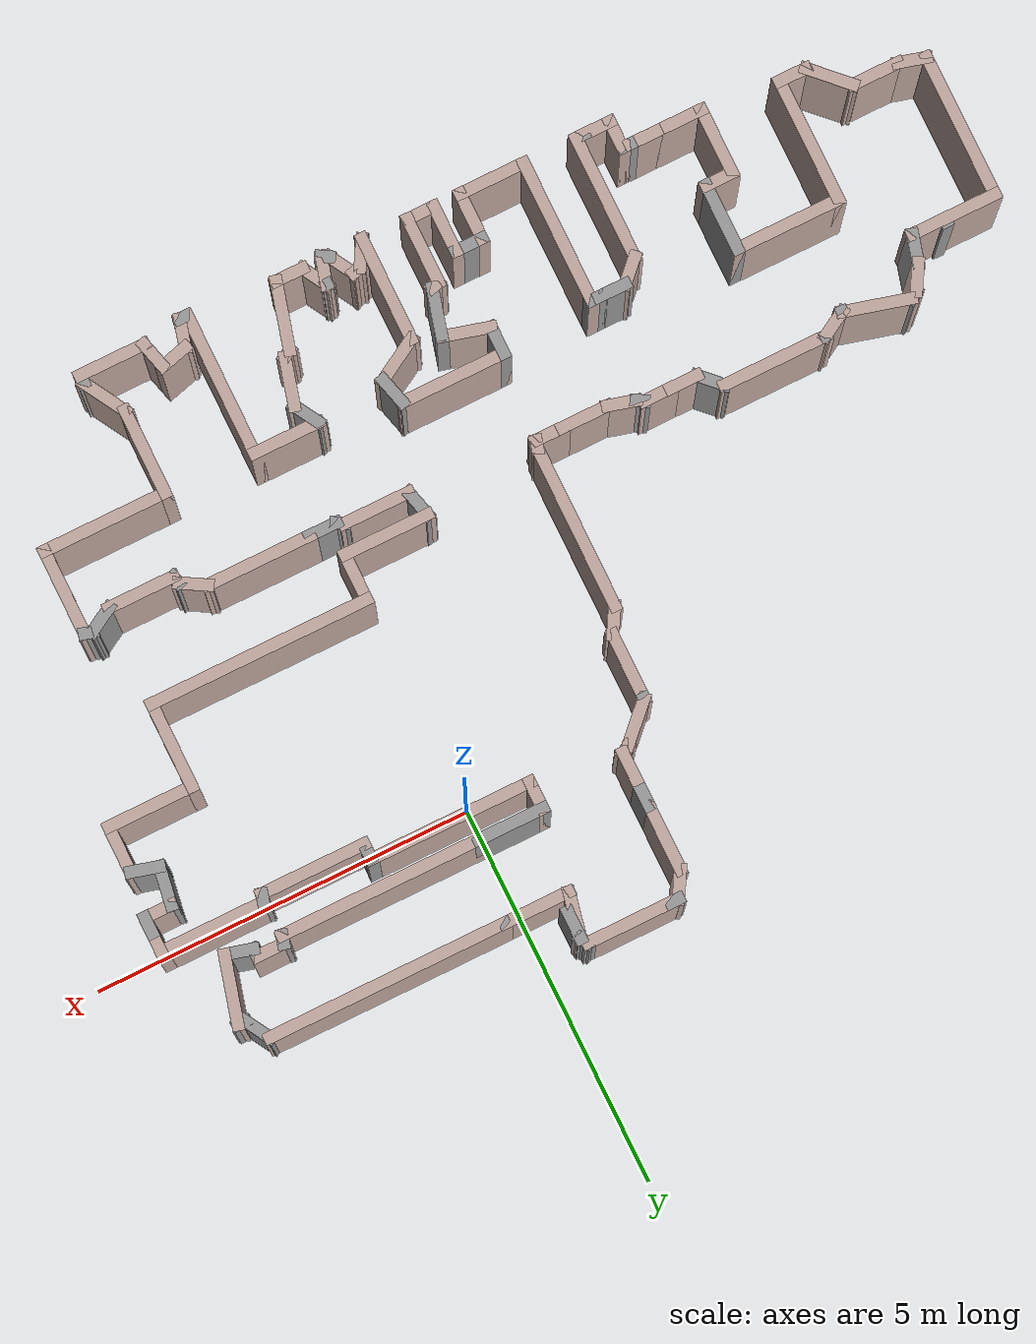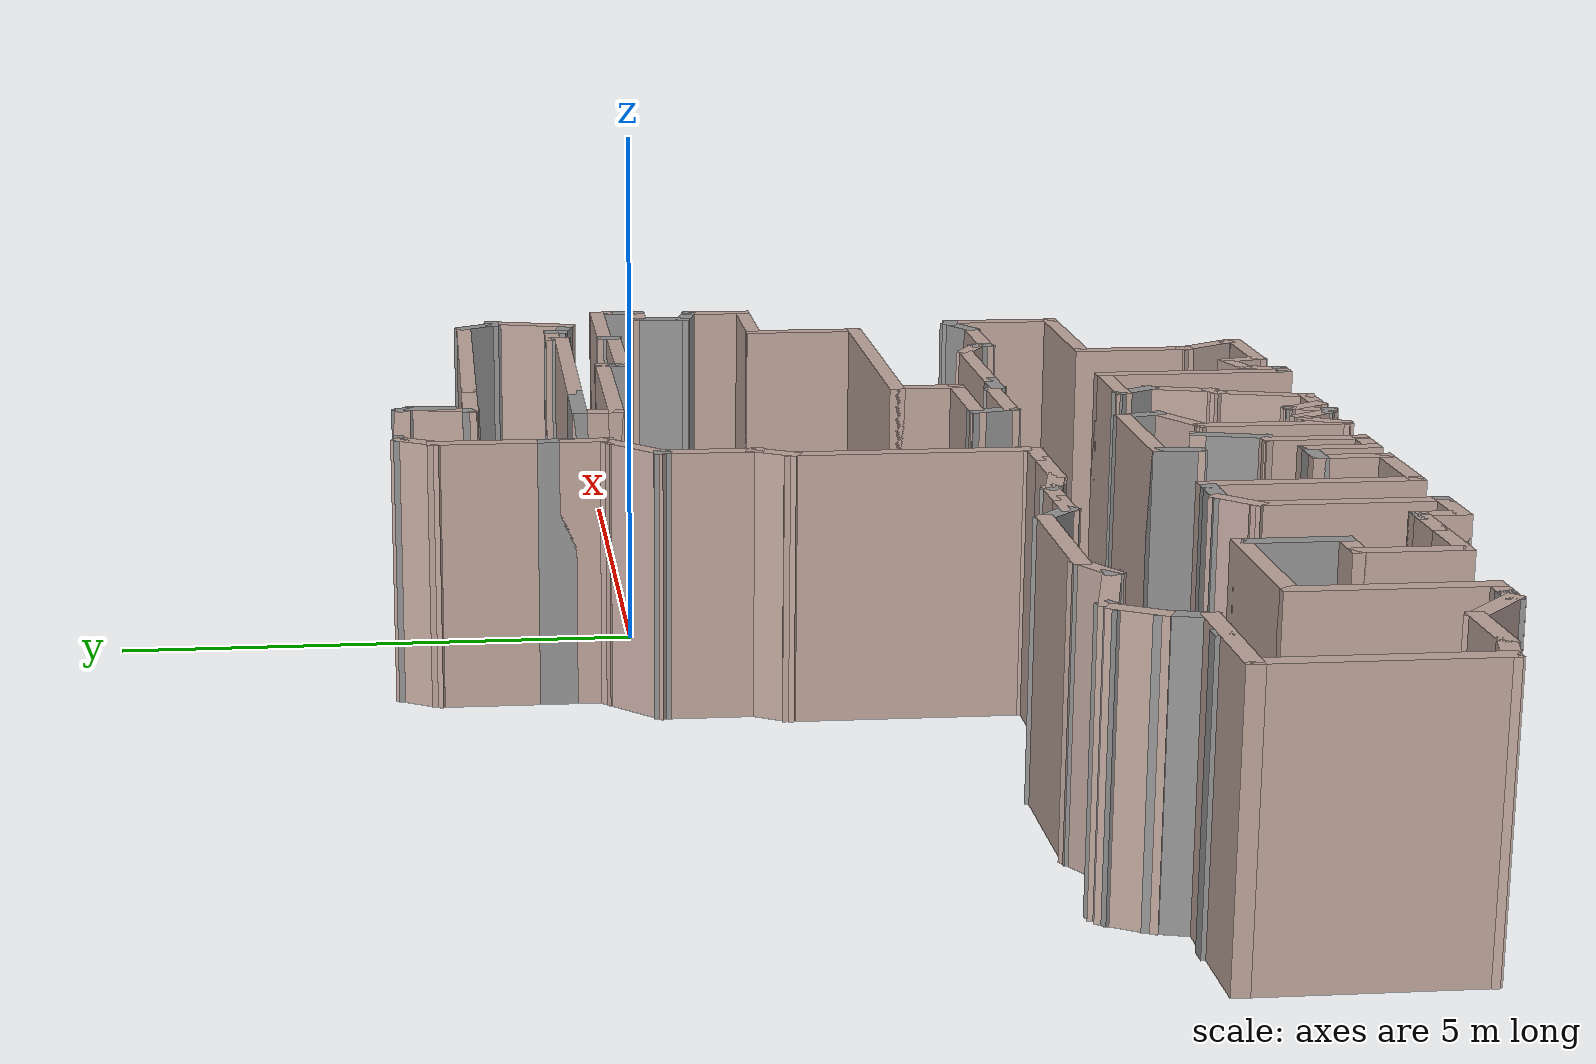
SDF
<?xml version='1.0'?>
<sdf version='1.6'>
  <model name='map_76'>
    <pose frame=''>-2.40102 -2.21939 0 0 -0 0</pose>
    <link name='Wall_1'>
      <collision name='Wall_1_Collision'>
        <geometry>
          <box>
            <size>0.5 0.15 2.5</size>
          </box>
        </geometry>
        <pose frame=''>0 0 1.25 0 -0 0</pose>
      </collision>
      <visual name='Wall_1_Visual'>
        <pose frame=''>0 0 1.25 0 -0 0</pose>
        <geometry>
          <box>
            <size>0.5 0.15 2.5</size>
          </box>
        </geometry>
        <material>
          <script>
            <uri>file://media/materials/scripts/gazebo.material</uri>
            <name>Gazebo/Grey</name>
          </script>
          <ambient>1 1 1 1</ambient>
        </material>
        <meta>
          <layer>0</layer>
        </meta>
      </visual>
      <pose frame=''>1.92491 4.16577 0 0 -0 1.5708</pose>
    </link>
    <link name='Wall_10'>
      <collision name='Wall_10_Collision'>
        <geometry>
          <box>
            <size>0.5 0.15 2.5</size>
          </box>
        </geometry>
        <pose frame=''>0 0 1.25 0 -0 0</pose>
      </collision>
      <visual name='Wall_10_Visual'>
        <pose frame=''>0 0 1.25 0 -0 0</pose>
        <geometry>
          <box>
            <size>0.5 0.15 2.5</size>
          </box>
        </geometry>
        <material>
          <script>
            <uri>file://media/materials/scripts/gazebo.material</uri>
            <name>Gazebo/Grey</name>
          </script>
          <ambient>0.760784 0.662745 0.627451 1</ambient>
        </material>
        <meta>
          <layer>0</layer>
        </meta>
      </visual>
      <pose frame=''>0.499907 2.74927 0 0 -0 -1.5708</pose>
    </link>
    <link name='Wall_100'>
      <collision name='Wall_100_Collision'>
        <geometry>
          <box>
            <size>0.75 0.15 2.5</size>
          </box>
        </geometry>
        <pose frame=''>0 0 1.25 0 -0 0</pose>
      </collision>
      <visual name='Wall_100_Visual'>
        <pose frame=''>0 0 1.25 0 -0 0</pose>
        <geometry>
          <box>
            <size>0.75 0.15 2.5</size>
          </box>
        </geometry>
        <material>
          <script>
            <uri>file://media/materials/scripts/gazebo.material</uri>
            <name>Gazebo/Grey</name>
          </script>
          <ambient>0.760784 0.662745 0.627451 1</ambient>
        </material>
        <meta>
          <layer>0</layer>
        </meta>
      </visual>
      <pose frame=''>4.1977 -3.98758 0 0 -0 2.0944</pose>
    </link>
    <link name='Wall_101'>
      <collision name='Wall_101_Collision'>
        <geometry>
          <box>
            <size>1.25 0.15 2.5</size>
          </box>
        </geometry>
        <pose frame=''>0 0 1.25 0 -0 0</pose>
      </collision>
      <visual name='Wall_101_Visual'>
        <pose frame=''>0 0 1.25 0 -0 0</pose>
        <geometry>
          <box>
            <size>1.25 0.15 2.5</size>
          </box>
        </geometry>
        <material>
          <script>
            <uri>file://media/materials/scripts/gazebo.material</uri>
            <name>Gazebo/Grey</name>
          </script>
          <ambient>0.760784 0.662745 0.627451 1</ambient>
        </material>
        <meta>
          <layer>0</layer>
        </meta>
      </visual>
      <pose frame=''>4.0477 -3.17777 0 0 -0 1.5708</pose>
    </link>
    <link name='Wall_104'>
      <collision name='Wall_104_Collision'>
        <geometry>
          <box>
            <size>1.75 0.15 2.5</size>
          </box>
        </geometry>
        <pose frame=''>0 0 1.25 0 -0 0</pose>
      </collision>
      <visual name='Wall_104_Visual'>
        <pose frame=''>0 0 1.25 0 -0 0</pose>
        <geometry>
          <box>
            <size>1.75 0.15 2.5</size>
          </box>
        </geometry>
        <material>
          <script>
            <uri>file://media/materials/scripts/gazebo.material</uri>
            <name>Gazebo/Grey</name>
          </script>
          <ambient>0.760784 0.662745 0.627451 1</ambient>
        </material>
        <meta>
          <layer>0</layer>
        </meta>
      </visual>
      <pose frame=''>4.8477 -2.62777 0 0 -0 0</pose>
    </link>
    <link name='Wall_105'>
      <collision name='Wall_105_Collision'>
        <geometry>
          <box>
            <size>1.25 0.15 2.5</size>
          </box>
        </geometry>
        <pose frame=''>0 0 1.25 0 -0 0</pose>
      </collision>
      <visual name='Wall_105_Visual'>
        <pose frame=''>0 0 1.25 0 -0 0</pose>
        <geometry>
          <box>
            <size>1.25 0.15 2.5</size>
          </box>
        </geometry>
        <material>
          <script>
            <uri>file://media/materials/scripts/gazebo.material</uri>
            <name>Gazebo/Grey</name>
          </script>
          <ambient>0.760784 0.662745 0.627451 1</ambient>
        </material>
        <meta>
          <layer>0</layer>
        </meta>
      </visual>
      <pose frame=''>5.6477 -2.07777 0 0 -0 1.5708</pose>
    </link>
    <link name='Wall_106'>
      <collision name='Wall_106_Collision'>
        <geometry>
          <box>
            <size>0.25 0.15 2.5</size>
          </box>
        </geometry>
        <pose frame=''>0 0 1.25 0 -0 0</pose>
      </collision>
      <visual name='Wall_106_Visual'>
        <pose frame=''>0 0 1.25 0 -0 0</pose>
        <geometry>
          <box>
            <size>0.25 0.15 2.5</size>
          </box>
        </geometry>
        <material>
          <script>
            <uri>file://media/materials/scripts/gazebo.material</uri>
            <name>Gazebo/Grey</name>
          </script>
          <ambient>1 1 1 1</ambient>
        </material>
        <meta>
          <layer>0</layer>
        </meta>
      </visual>
      <pose frame=''>5.59941 -1.51483 0 0 -0 2.87979</pose>
    </link>
    <link name='Wall_107'>
      <collision name='Wall_107_Collision'>
        <geometry>
          <box>
            <size>0.5 0.15 2.5</size>
          </box>
        </geometry>
        <pose frame=''>0 0 1.25 0 -0 0</pose>
      </collision>
      <visual name='Wall_107_Visual'>
        <pose frame=''>0 0 1.25 0 -0 0</pose>
        <geometry>
          <box>
            <size>0.5 0.15 2.5</size>
          </box>
        </geometry>
        <material>
          <script>
            <uri>file://media/materials/scripts/gazebo.material</uri>
            <name>Gazebo/Grey</name>
          </script>
          <ambient>1 1 1 1</ambient>
        </material>
        <meta>
          <layer>0</layer>
        </meta>
      </visual>
      <pose frame=''>5.39956 -1.58939 0 0 -0 -2.61799</pose>
    </link>
    <link name='Wall_108'>
      <collision name='Wall_108_Collision'>
        <geometry>
          <box>
            <size>1 0.15 2.5</size>
          </box>
        </geometry>
        <pose frame=''>0 0 1.25 0 -0 0</pose>
      </collision>
      <visual name='Wall_108_Visual'>
        <pose frame=''>0 0 1.25 0 -0 0</pose>
        <geometry>
          <box>
            <size>1 0.15 2.5</size>
          </box>
        </geometry>
        <material>
          <script>
            <uri>file://media/materials/scripts/gazebo.material</uri>
            <name>Gazebo/Grey</name>
          </script>
          <ambient>0.760784 0.662745 0.627451 1</ambient>
        </material>
        <meta>
          <layer>0</layer>
        </meta>
      </visual>
      <pose frame=''>4.823 -1.67689 0 0 -0 3.14159</pose>
    </link>
    <link name='Wall_109'>
      <collision name='Wall_109_Collision'>
        <geometry>
          <box>
            <size>0.25 0.15 2.5</size>
          </box>
        </geometry>
        <pose frame=''>0 0 1.25 0 -0 0</pose>
      </collision>
      <visual name='Wall_109_Visual'>
        <pose frame=''>0 0 1.25 0 -0 0</pose>
        <geometry>
          <box>
            <size>0.25 0.15 2.5</size>
          </box>
        </geometry>
        <material>
          <script>
            <uri>file://media/materials/scripts/gazebo.material</uri>
            <name>Gazebo/Grey</name>
          </script>
          <ambient>1 1 1 1</ambient>
        </material>
        <meta>
          <layer>0</layer>
        </meta>
      </visual>
      <pose frame=''>4.38506 -1.62859 0 0 -0 1.8326</pose>
    </link>
    <link name='Wall_11'>
      <collision name='Wall_11_Collision'>
        <geometry>
          <box>
            <size>0.25 0.15 2.5</size>
          </box>
        </geometry>
        <pose frame=''>0 0 1.25 0 -0 0</pose>
      </collision>
      <visual name='Wall_11_Visual'>
        <pose frame=''>0 0 1.25 0 -0 0</pose>
        <geometry>
          <box>
            <size>0.25 0.15 2.5</size>
          </box>
        </geometry>
        <material>
          <script>
            <uri>file://media/materials/scripts/gazebo.material</uri>
            <name>Gazebo/Grey</name>
          </script>
          <ambient>0.760784 0.662745 0.627451 1</ambient>
        </material>
        <meta>
          <layer>0</layer>
        </meta>
      </visual>
      <pose frame=''>0.456606 2.54927 0 0 -0 -2.61799</pose>
    </link>
    <link name='Wall_110'>
      <collision name='Wall_110_Collision'>
        <geometry>
          <box>
            <size>0.5 0.15 2.5</size>
          </box>
        </geometry>
        <pose frame=''>0 0 1.25 0 -0 0</pose>
      </collision>
      <visual name='Wall_110_Visual'>
        <pose frame=''>0 0 1.25 0 -0 0</pose>
        <geometry>
          <box>
            <size>0.5 0.15 2.5</size>
          </box>
        </geometry>
        <material>
          <script>
            <uri>file://media/materials/scripts/gazebo.material</uri>
            <name>Gazebo/Grey</name>
          </script>
          <ambient>0.760784 0.662745 0.627451 1</ambient>
        </material>
        <meta>
          <layer>0</layer>
        </meta>
      </visual>
      <pose frame=''>4.22057 -1.4928 0 0 -0 2.61799</pose>
    </link>
    <link name='Wall_111'>
      <collision name='Wall_111_Collision'>
        <geometry>
          <box>
            <size>1.5 0.15 2.5</size>
          </box>
        </geometry>
        <pose frame=''>0 0 1.25 0 -0 0</pose>
      </collision>
      <visual name='Wall_111_Visual'>
        <pose frame=''>0 0 1.25 0 -0 0</pose>
        <geometry>
          <box>
            <size>1.5 0.15 2.5</size>
          </box>
        </geometry>
        <material>
          <script>
            <uri>file://media/materials/scripts/gazebo.material</uri>
            <name>Gazebo/Grey</name>
          </script>
          <ambient>0.760784 0.662745 0.627451 1</ambient>
        </material>
        <meta>
          <layer>0</layer>
        </meta>
      </visual>
      <pose frame=''>3.39401 -1.40529 0 0 -0 3.14159</pose>
    </link>
    <link name='Wall_112'>
      <collision name='Wall_112_Collision'>
        <geometry>
          <box>
            <size>0.5 0.15 2.5</size>
          </box>
        </geometry>
        <pose frame=''>0 0 1.25 0 -0 0</pose>
      </collision>
      <visual name='Wall_112_Visual'>
        <pose frame=''>0 0 1.25 0 -0 0</pose>
        <geometry>
          <box>
            <size>0.5 0.15 2.5</size>
          </box>
        </geometry>
        <material>
          <script>
            <uri>file://media/materials/scripts/gazebo.material</uri>
            <name>Gazebo/Grey</name>
          </script>
          <ambient>1 1 1 1</ambient>
        </material>
        <meta>
          <layer>0</layer>
        </meta>
      </visual>
      <pose frame=''>2.54401 -1.40529 0 0 -0 3.14159</pose>
    </link>
    <link name='Wall_113'>
      <collision name='Wall_113_Collision'>
        <geometry>
          <box>
            <size>0.25 0.15 2.5</size>
          </box>
        </geometry>
        <pose frame=''>0 0 1.25 0 -0 0</pose>
      </collision>
      <visual name='Wall_113_Visual'>
        <pose frame=''>0 0 1.25 0 -0 0</pose>
        <geometry>
          <box>
            <size>0.25 0.15 2.5</size>
          </box>
        </geometry>
        <material>
          <script>
            <uri>file://media/materials/scripts/gazebo.material</uri>
            <name>Gazebo/Grey</name>
          </script>
          <ambient>1 1 1 1</ambient>
        </material>
        <meta>
          <layer>0</layer>
        </meta>
      </visual>
      <pose frame=''>2.32571 -1.3803 0 0 -0 2.61799</pose>
    </link>
    <link name='Wall_114'>
      <collision name='Wall_114_Collision'>
        <geometry>
          <box>
            <size>1 0.15 2.5</size>
          </box>
        </geometry>
        <pose frame=''>0 0 1.25 0 -0 0</pose>
      </collision>
      <visual name='Wall_114_Visual'>
        <pose frame=''>0 0 1.25 0 -0 0</pose>
        <geometry>
          <box>
            <size>1 0.15 2.5</size>
          </box>
        </geometry>
        <material>
          <script>
            <uri>file://media/materials/scripts/gazebo.material</uri>
            <name>Gazebo/Grey</name>
          </script>
          <ambient>0.760784 0.662745 0.627451 1</ambient>
        </material>
        <meta>
          <layer>0</layer>
        </meta>
      </visual>
      <pose frame=''>1.85741 -1.35529 0 0 -0 3.14159</pose>
    </link>
    <link name='Wall_115'>
      <collision name='Wall_115_Collision'>
        <geometry>
          <box>
            <size>0.5 0.15 2.5</size>
          </box>
        </geometry>
        <pose frame=''>0 0 1.25 0 -0 0</pose>
      </collision>
      <visual name='Wall_115_Visual'>
        <pose frame=''>0 0 1.25 0 -0 0</pose>
        <geometry>
          <box>
            <size>0.5 0.15 2.5</size>
          </box>
        </geometry>
        <material>
          <script>
            <uri>file://media/materials/scripts/gazebo.material</uri>
            <name>Gazebo/Grey</name>
          </script>
          <ambient>1 1 1 1</ambient>
        </material>
        <meta>
          <layer>0</layer>
        </meta>
      </visual>
      <pose frame=''>1.38712 -1.18626 0 0 -0 1.8326</pose>
    </link>
    <link name='Wall_116'>
      <collision name='Wall_116_Collision'>
        <geometry>
          <box>
            <size>1.25 0.15 2.5</size>
          </box>
        </geometry>
        <pose frame=''>0 0 1.25 0 -0 0</pose>
      </collision>
      <visual name='Wall_116_Visual'>
        <pose frame=''>0 0 1.25 0 -0 0</pose>
        <geometry>
          <box>
            <size>1.25 0.15 2.5</size>
          </box>
        </geometry>
        <material>
          <script>
            <uri>file://media/materials/scripts/gazebo.material</uri>
            <name>Gazebo/Grey</name>
          </script>
          <ambient>0.760784 0.662745 0.627451 1</ambient>
        </material>
        <meta>
          <layer>0</layer>
        </meta>
      </visual>
      <pose frame=''>1.89182 -1.01722 0 0 -0 0</pose>
    </link>
    <link name='Wall_117'>
      <collision name='Wall_117_Collision'>
        <geometry>
          <box>
            <size>0.75 0.15 2.5</size>
          </box>
        </geometry>
        <pose frame=''>0 0 1.25 0 -0 0</pose>
      </collision>
      <visual name='Wall_117_Visual'>
        <pose frame=''>0 0 1.25 0 -0 0</pose>
        <geometry>
          <box>
            <size>0.75 0.15 2.5</size>
          </box>
        </geometry>
        <material>
          <script>
            <uri>file://media/materials/scripts/gazebo.material</uri>
            <name>Gazebo/Grey</name>
          </script>
          <ambient>0.760784 0.662745 0.627451 1</ambient>
        </material>
        <meta>
          <layer>0</layer>
        </meta>
      </visual>
      <pose frame=''>2.44182 -0.717221 0 0 -0 1.5708</pose>
    </link>
    <link name='Wall_118'>
      <collision name='Wall_118_Collision'>
        <geometry>
          <box>
            <size>3 0.15 2.5</size>
          </box>
        </geometry>
        <pose frame=''>0 0 1.25 0 -0 0</pose>
      </collision>
      <visual name='Wall_118_Visual'>
        <pose frame=''>0 0 1.25 0 -0 0</pose>
        <geometry>
          <box>
            <size>3 0.15 2.5</size>
          </box>
        </geometry>
        <material>
          <script>
            <uri>file://media/materials/scripts/gazebo.material</uri>
            <name>Gazebo/Grey</name>
          </script>
          <ambient>0.760784 0.662745 0.627451 1</ambient>
        </material>
        <meta>
          <layer>0</layer>
        </meta>
      </visual>
      <pose frame=''>3.86682 -0.417221 0 0 -0 0</pose>
    </link>
    <link name='Wall_12'>
      <collision name='Wall_12_Collision'>
        <geometry>
          <box>
            <size>0.75 0.15 2.5</size>
          </box>
        </geometry>
        <pose frame=''>0 0 1.25 0 -0 0</pose>
      </collision>
      <visual name='Wall_12_Visual'>
        <pose frame=''>0 0 1.25 0 -0 0</pose>
        <geometry>
          <box>
            <size>0.75 0.15 2.5</size>
          </box>
        </geometry>
        <material>
          <script>
            <uri>file://media/materials/scripts/gazebo.material</uri>
            <name>Gazebo/Grey</name>
          </script>
          <ambient>0.760784 0.662745 0.627451 1</ambient>
        </material>
        <meta>
          <layer>0</layer>
        </meta>
      </visual>
      <pose frame=''>0.201173 2.31214 0 0 -0 -2.35619</pose>
    </link>
    <link name='Wall_121'>
      <collision name='Wall_121_Collision'>
        <geometry>
          <box>
            <size>1.25 0.15 2.5</size>
          </box>
        </geometry>
        <pose frame=''>0 0 1.25 0 -0 0</pose>
      </collision>
      <visual name='Wall_121_Visual'>
        <pose frame=''>0 0 1.25 0 -0 0</pose>
        <geometry>
          <box>
            <size>1.25 0.15 2.5</size>
          </box>
        </geometry>
        <material>
          <script>
            <uri>file://media/materials/scripts/gazebo.material</uri>
            <name>Gazebo/Grey</name>
          </script>
          <ambient>0.760784 0.662745 0.627451 1</ambient>
        </material>
        <meta>
          <layer>0</layer>
        </meta>
      </visual>
      <pose frame=''>5.29182 0.132779 0 0 -0 1.5708</pose>
    </link>
    <link name='Wall_122'>
      <collision name='Wall_122_Collision'>
        <geometry>
          <box>
            <size>1.25 0.15 2.5</size>
          </box>
        </geometry>
        <pose frame=''>0 0 1.25 0 -0 0</pose>
      </collision>
      <visual name='Wall_122_Visual'>
        <pose frame=''>0 0 1.25 0 -0 0</pose>
        <geometry>
          <box>
            <size>1.25 0.15 2.5</size>
          </box>
        </geometry>
        <material>
          <script>
            <uri>file://media/materials/scripts/gazebo.material</uri>
            <name>Gazebo/Grey</name>
          </script>
          <ambient>0.760784 0.662745 0.627451 1</ambient>
        </material>
        <meta>
          <layer>0</layer>
        </meta>
      </visual>
      <pose frame=''>5.84182 0.682779 0 0 -0 0</pose>
    </link>
    <link name='Wall_125'>
      <collision name='Wall_125_Collision'>
        <geometry>
          <box>
            <size>0.75 0.15 2.5</size>
          </box>
        </geometry>
        <pose frame=''>0 0 1.25 0 -0 0</pose>
      </collision>
      <visual name='Wall_125_Visual'>
        <pose frame=''>0 0 1.25 0 -0 0</pose>
        <geometry>
          <box>
            <size>0.75 0.15 2.5</size>
          </box>
        </geometry>
        <material>
          <script>
            <uri>file://media/materials/scripts/gazebo.material</uri>
            <name>Gazebo/Grey</name>
          </script>
          <ambient>0.760784 0.662745 0.627451 1</ambient>
        </material>
        <meta>
          <layer>0</layer>
        </meta>
      </visual>
      <pose frame=''>6.39182 0.982779 0 0 -0 1.5708</pose>
    </link>
    <link name='Wall_126'>
      <collision name='Wall_126_Collision'>
        <geometry>
          <box>
            <size>0.5 0.15 2.5</size>
          </box>
        </geometry>
        <pose frame=''>0 0 1.25 0 -0 0</pose>
      </collision>
      <visual name='Wall_126_Visual'>
        <pose frame=''>0 0 1.25 0 -0 0</pose>
        <geometry>
          <box>
            <size>0.5 0.15 2.5</size>
          </box>
        </geometry>
        <material>
          <script>
            <uri>file://media/materials/scripts/gazebo.material</uri>
            <name>Gazebo/Grey</name>
          </script>
          <ambient>1 1 1 1</ambient>
        </material>
        <meta>
          <layer>0</layer>
        </meta>
      </visual>
      <pose frame=''>6.22279 1.32807 0 0 -0 2.87979</pose>
    </link>
    <link name='Wall_129'>
      <collision name='Wall_129_Collision'>
        <geometry>
          <box>
            <size>0.5 0.15 2.5</size>
          </box>
        </geometry>
        <pose frame=''>0 0 1.25 0 -0 0</pose>
      </collision>
      <visual name='Wall_129_Visual'>
        <pose frame=''>0 0 1.25 0 -0 0</pose>
        <geometry>
          <box>
            <size>0.5 0.15 2.5</size>
          </box>
        </geometry>
        <material>
          <script>
            <uri>file://media/materials/scripts/gazebo.material</uri>
            <name>Gazebo/Grey</name>
          </script>
          <ambient>0.760784 0.662745 0.627451 1</ambient>
        </material>
        <meta>
          <layer>0</layer>
        </meta>
      </visual>
      <pose frame=''>6.3022 1.84721 0 0 -0 0</pose>
    </link>
    <link name='Wall_13'>
      <collision name='Wall_13_Collision'>
        <geometry>
          <box>
            <size>0.15 0.15 2.5</size>
          </box>
        </geometry>
        <pose frame=''>0 0 1.25 0 -0 0</pose>
      </collision>
      <visual name='Wall_13_Visual'>
        <pose frame=''>0 0 1.25 0 -0 0</pose>
        <geometry>
          <box>
            <size>0.15 0.15 2.5</size>
          </box>
        </geometry>
        <material>
          <script>
            <uri>file://media/materials/scripts/gazebo.material</uri>
            <name>Gazebo/Grey</name>
          </script>
          <ambient>1 1 1 1</ambient>
        </material>
        <meta>
          <layer>0</layer>
        </meta>
      </visual>
      <pose frame=''>-0.010959 2.1 0 0 -0 0</pose>
    </link>
    <link name='Wall_130'>
      <collision name='Wall_130_Collision'>
        <geometry>
          <box>
            <size>0.5 0.15 2.5</size>
          </box>
        </geometry>
        <pose frame=''>0 0 1.25 0 -0 0</pose>
      </collision>
      <visual name='Wall_130_Visual'>
        <pose frame=''>0 0 1.25 0 -0 0</pose>
        <geometry>
          <box>
            <size>0.5 0.15 2.5</size>
          </box>
        </geometry>
        <material>
          <script>
            <uri>file://media/materials/scripts/gazebo.material</uri>
            <name>Gazebo/Grey</name>
          </script>
          <ambient>1 1 1 1</ambient>
        </material>
        <meta>
          <layer>0</layer>
        </meta>
      </visual>
      <pose frame=''>6.4772 2.02221 0 0 -0 1.5708</pose>
    </link>
    <link name='Wall_131'>
      <collision name='Wall_131_Collision'>
        <geometry>
          <box>
            <size>0.15 0.15 2.5</size>
          </box>
        </geometry>
        <pose frame=''>0 0 1.25 0 -0 0</pose>
      </collision>
      <visual name='Wall_131_Visual'>
        <pose frame=''>0 0 1.25 0 -0 0</pose>
        <geometry>
          <box>
            <size>0.15 0.15 2.5</size>
          </box>
        </geometry>
        <material>
          <script>
            <uri>file://media/materials/scripts/gazebo.material</uri>
            <name>Gazebo/Grey</name>
          </script>
          <ambient>1 1 1 1</ambient>
        </material>
        <meta>
          <layer>0</layer>
        </meta>
      </visual>
      <pose frame=''>6.4772 2.19721 0 0 -0 0</pose>
    </link>
    <link name='Wall_133'>
      <collision name='Wall_133_Collision'>
        <geometry>
          <box>
            <size>0.25 0.15 2.5</size>
          </box>
        </geometry>
        <pose frame=''>0 0 1.25 0 -0 0</pose>
      </collision>
      <visual name='Wall_133_Visual'>
        <pose frame=''>0 0 1.25 0 -0 0</pose>
        <geometry>
          <box>
            <size>0.25 0.15 2.5</size>
          </box>
        </geometry>
        <material>
          <script>
            <uri>file://media/materials/scripts/gazebo.material</uri>
            <name>Gazebo/Grey</name>
          </script>
          <ambient>0.760784 0.662745 0.627451 1</ambient>
        </material>
        <meta>
          <layer>0</layer>
        </meta>
      </visual>
      <pose frame=''>6.4772 2.24721 0 0 -0 1.5708</pose>
    </link>
    <link name='Wall_134'>
      <collision name='Wall_134_Collision'>
        <geometry>
          <box>
            <size>1.5 0.15 2.5</size>
          </box>
        </geometry>
        <pose frame=''>0 0 1.25 0 -0 0</pose>
      </collision>
      <visual name='Wall_134_Visual'>
        <pose frame=''>0 0 1.25 0 -0 0</pose>
        <geometry>
          <box>
            <size>1.5 0.15 2.5</size>
          </box>
        </geometry>
        <material>
          <script>
            <uri>file://media/materials/scripts/gazebo.material</uri>
            <name>Gazebo/Grey</name>
          </script>
          <ambient>0.760784 0.662745 0.627451 1</ambient>
        </material>
        <meta>
          <layer>0</layer>
        </meta>
      </visual>
      <pose frame=''>5.8022 2.29721 0 0 -0 3.14159</pose>
    </link>
    <link name='Wall_135'>
      <collision name='Wall_135_Collision'>
        <geometry>
          <box>
            <size>0.25 0.15 2.5</size>
          </box>
        </geometry>
        <pose frame=''>0 0 1.25 0 -0 0</pose>
      </collision>
      <visual name='Wall_135_Visual'>
        <pose frame=''>0 0 1.25 0 -0 0</pose>
        <geometry>
          <box>
            <size>0.25 0.15 2.5</size>
          </box>
        </geometry>
        <material>
          <script>
            <uri>file://media/materials/scripts/gazebo.material</uri>
            <name>Gazebo/Grey</name>
          </script>
          <ambient>1 1 1 1</ambient>
        </material>
        <meta>
          <layer>0</layer>
        </meta>
      </visual>
      <pose frame=''>5.11425 2.24892 0 0 -0 -1.8326</pose>
    </link>
    <link name='Wall_136'>
      <collision name='Wall_136_Collision'>
        <geometry>
          <box>
            <size>1.5 0.15 2.5</size>
          </box>
        </geometry>
        <pose frame=''>0 0 1.25 0 -0 0</pose>
      </collision>
      <visual name='Wall_136_Visual'>
        <pose frame=''>0 0 1.25 0 -0 0</pose>
        <geometry>
          <box>
            <size>1.5 0.15 2.5</size>
          </box>
        </geometry>
        <material>
          <script>
            <uri>file://media/materials/scripts/gazebo.material</uri>
            <name>Gazebo/Grey</name>
          </script>
          <ambient>0.760784 0.662745 0.627451 1</ambient>
        </material>
        <meta>
          <layer>0</layer>
        </meta>
      </visual>
      <pose frame=''>4.42631 2.20062 0 0 -0 3.14159</pose>
    </link>
    <link name='Wall_137'>
      <collision name='Wall_137_Collision'>
        <geometry>
          <box>
            <size>0.25 0.15 2.5</size>
          </box>
        </geometry>
        <pose frame=''>0 0 1.25 0 -0 0</pose>
      </collision>
      <visual name='Wall_137_Visual'>
        <pose frame=''>0 0 1.25 0 -0 0</pose>
        <geometry>
          <box>
            <size>0.25 0.15 2.5</size>
          </box>
        </geometry>
        <material>
          <script>
            <uri>file://media/materials/scripts/gazebo.material</uri>
            <name>Gazebo/Grey</name>
          </script>
          <ambient>1 1 1 1</ambient>
        </material>
        <meta>
          <layer>0</layer>
        </meta>
      </visual>
      <pose frame=''>3.75131 2.25062 0 0 -0 1.5708</pose>
    </link>
    <link name='Wall_138'>
      <collision name='Wall_138_Collision'>
        <geometry>
          <box>
            <size>0.25 0.15 2.5</size>
          </box>
        </geometry>
        <pose frame=''>0 0 1.25 0 -0 0</pose>
      </collision>
      <visual name='Wall_138_Visual'>
        <pose frame=''>0 0 1.25 0 -0 0</pose>
        <geometry>
          <box>
            <size>0.25 0.15 2.5</size>
          </box>
        </geometry>
        <material>
          <script>
            <uri>file://media/materials/scripts/gazebo.material</uri>
            <name>Gazebo/Grey</name>
          </script>
          <ambient>1 1 1 1</ambient>
        </material>
        <meta>
          <layer>0</layer>
        </meta>
      </visual>
      <pose frame=''>3.75131 2.35062 0 0 -0 1.5708</pose>
    </link>
    <link name='Wall_139'>
      <collision name='Wall_139_Collision'>
        <geometry>
          <box>
            <size>2.25 0.15 2.5</size>
          </box>
        </geometry>
        <pose frame=''>0 0 1.25 0 -0 0</pose>
      </collision>
      <visual name='Wall_139_Visual'>
        <pose frame=''>0 0 1.25 0 -0 0</pose>
        <geometry>
          <box>
            <size>2.25 0.15 2.5</size>
          </box>
        </geometry>
        <material>
          <script>
            <uri>file://media/materials/scripts/gazebo.material</uri>
            <name>Gazebo/Grey</name>
          </script>
          <ambient>0.760784 0.662745 0.627451 1</ambient>
        </material>
        <meta>
          <layer>0</layer>
        </meta>
      </visual>
      <pose frame=''>2.70131 2.40062 0 0 -0 3.14159</pose>
    </link>
    <link name='Wall_14'>
      <collision name='Wall_14_Collision'>
        <geometry>
          <box>
            <size>1 0.15 2.5</size>
          </box>
        </geometry>
        <pose frame=''>0 0 1.25 0 -0 0</pose>
      </collision>
      <visual name='Wall_14_Visual'>
        <pose frame=''>0 0 1.25 0 -0 0</pose>
        <geometry>
          <box>
            <size>1 0.15 2.5</size>
          </box>
        </geometry>
        <material>
          <script>
            <uri>file://media/materials/scripts/gazebo.material</uri>
            <name>Gazebo/Grey</name>
          </script>
          <ambient>0.760784 0.662745 0.627451 1</ambient>
        </material>
        <meta>
          <layer>0</layer>
        </meta>
      </visual>
      <pose frame=''>-0.010959 1.675 0 0 -0 -1.5708</pose>
    </link>
    <link name='Wall_140'>
      <collision name='Wall_140_Collision'>
        <geometry>
          <box>
            <size>0.5 0.15 2.5</size>
          </box>
        </geometry>
        <pose frame=''>0 0 1.25 0 -0 0</pose>
      </collision>
      <visual name='Wall_140_Visual'>
        <pose frame=''>0 0 1.25 0 -0 0</pose>
        <geometry>
          <box>
            <size>0.5 0.15 2.5</size>
          </box>
        </geometry>
        <material>
          <script>
            <uri>file://media/materials/scripts/gazebo.material</uri>
            <name>Gazebo/Grey</name>
          </script>
          <ambient>0.760784 0.662745 0.627451 1</ambient>
        </material>
        <meta>
          <layer>0</layer>
        </meta>
      </visual>
      <pose frame=''>1.65131 2.57562 0 0 -0 1.5708</pose>
    </link>
    <link name='Wall_141'>
      <collision name='Wall_141_Collision'>
        <geometry>
          <box>
            <size>1 0.15 2.5</size>
          </box>
        </geometry>
        <pose frame=''>0 0 1.25 0 -0 0</pose>
      </collision>
      <visual name='Wall_141_Visual'>
        <pose frame=''>0 0 1.25 0 -0 0</pose>
        <geometry>
          <box>
            <size>1 0.15 2.5</size>
          </box>
        </geometry>
        <material>
          <script>
            <uri>file://media/materials/scripts/gazebo.material</uri>
            <name>Gazebo/Grey</name>
          </script>
          <ambient>1 1 1 1</ambient>
        </material>
        <meta>
          <layer>0</layer>
        </meta>
      </visual>
      <pose frame=''>2.07631 2.75062 0 0 -0 0</pose>
    </link>
    <link name='Wall_142'>
      <collision name='Wall_142_Collision'>
        <geometry>
          <box>
            <size>2.75 0.15 2.5</size>
          </box>
        </geometry>
        <pose frame=''>0 0 1.25 0 -0 0</pose>
      </collision>
      <visual name='Wall_142_Visual'>
        <pose frame=''>0 0 1.25 0 -0 0</pose>
        <geometry>
          <box>
            <size>2.75 0.15 2.5</size>
          </box>
        </geometry>
        <material>
          <script>
            <uri>file://media/materials/scripts/gazebo.material</uri>
            <name>Gazebo/Grey</name>
          </script>
          <ambient>0.760784 0.662745 0.627451 1</ambient>
        </material>
        <meta>
          <layer>0</layer>
        </meta>
      </visual>
      <pose frame=''>3.80131 2.75062 0 0 -0 0</pose>
    </link>
    <link name='Wall_143'>
      <collision name='Wall_143_Collision'>
        <geometry>
          <box>
            <size>0.25 0.15 2.5</size>
          </box>
        </geometry>
        <pose frame=''>0 0 1.25 0 -0 0</pose>
      </collision>
      <visual name='Wall_143_Visual'>
        <pose frame=''>0 0 1.25 0 -0 0</pose>
        <geometry>
          <box>
            <size>0.25 0.15 2.5</size>
          </box>
        </geometry>
        <material>
          <script>
            <uri>file://media/materials/scripts/gazebo.material</uri>
            <name>Gazebo/Grey</name>
          </script>
          <ambient>1 1 1 1</ambient>
        </material>
        <meta>
          <layer>0</layer>
        </meta>
      </visual>
      <pose frame=''>5.11425 2.79892 0 0 -0 1.309</pose>
    </link>
    <link name='Wall_144'>
      <collision name='Wall_144_Collision'>
        <geometry>
          <box>
            <size>0.5 0.15 2.5</size>
          </box>
        </geometry>
        <pose frame=''>0 0 1.25 0 -0 0</pose>
      </collision>
      <visual name='Wall_144_Visual'>
        <pose frame=''>0 0 1.25 0 -0 0</pose>
        <geometry>
          <box>
            <size>0.5 0.15 2.5</size>
          </box>
        </geometry>
        <material>
          <script>
            <uri>file://media/materials/scripts/gazebo.material</uri>
            <name>Gazebo/Grey</name>
          </script>
          <ambient>0.760784 0.662745 0.627451 1</ambient>
        </material>
        <meta>
          <layer>0</layer>
        </meta>
      </visual>
      <pose frame=''>5.3022 2.84721 0 0 -0 0</pose>
    </link>
    <link name='Wall_145'>
      <collision name='Wall_145_Collision'>
        <geometry>
          <box>
            <size>0.25 0.15 2.5</size>
          </box>
        </geometry>
        <pose frame=''>0 0 1.25 0 -0 0</pose>
      </collision>
      <visual name='Wall_145_Visual'>
        <pose frame=''>0 0 1.25 0 -0 0</pose>
        <geometry>
          <box>
            <size>0.25 0.15 2.5</size>
          </box>
        </geometry>
        <material>
          <script>
            <uri>file://media/materials/scripts/gazebo.material</uri>
            <name>Gazebo/Grey</name>
          </script>
          <ambient>1 1 1 1</ambient>
        </material>
        <meta>
          <layer>0</layer>
        </meta>
      </visual>
      <pose frame=''>5.4772 2.79721 0 0 -0 -1.5708</pose>
    </link>
    <link name='Wall_146'>
      <collision name='Wall_146_Collision'>
        <geometry>
          <box>
            <size>0.5 0.15 2.5</size>
          </box>
        </geometry>
        <pose frame=''>0 0 1.25 0 -0 0</pose>
      </collision>
      <visual name='Wall_146_Visual'>
        <pose frame=''>0 0 1.25 0 -0 0</pose>
        <geometry>
          <box>
            <size>0.5 0.15 2.5</size>
          </box>
        </geometry>
        <material>
          <script>
            <uri>file://media/materials/scripts/gazebo.material</uri>
            <name>Gazebo/Grey</name>
          </script>
          <ambient>1 1 1 1</ambient>
        </material>
        <meta>
          <layer>0</layer>
        </meta>
      </visual>
      <pose frame=''>5.64623 2.70192 0 0 -0 -0.261799</pose>
    </link>
    <link name='Wall_147'>
      <collision name='Wall_147_Collision'>
        <geometry>
          <box>
            <size>1 0.15 2.5</size>
          </box>
        </geometry>
        <pose frame=''>0 0 1.25 0 -0 0</pose>
      </collision>
      <visual name='Wall_147_Visual'>
        <pose frame=''>0 0 1.25 0 -0 0</pose>
        <geometry>
          <box>
            <size>1 0.15 2.5</size>
          </box>
        </geometry>
        <material>
          <script>
            <uri>file://media/materials/scripts/gazebo.material</uri>
            <name>Gazebo/Grey</name>
          </script>
          <ambient>0.760784 0.662745 0.627451 1</ambient>
        </material>
        <meta>
          <layer>0</layer>
        </meta>
      </visual>
      <pose frame=''>5.92527 3.06714 0 0 -0 1.309</pose>
    </link>
    <link name='Wall_148'>
      <collision name='Wall_148_Collision'>
        <geometry>
          <box>
            <size>0.25 0.15 2.5</size>
          </box>
        </geometry>
        <pose frame=''>0 0 1.25 0 -0 0</pose>
      </collision>
      <visual name='Wall_148_Visual'>
        <pose frame=''>0 0 1.25 0 -0 0</pose>
        <geometry>
          <box>
            <size>0.25 0.15 2.5</size>
          </box>
        </geometry>
        <material>
          <script>
            <uri>file://media/materials/scripts/gazebo.material</uri>
            <name>Gazebo/Grey</name>
          </script>
          <ambient>1 1 1 1</ambient>
        </material>
        <meta>
          <layer>0</layer>
        </meta>
      </visual>
      <pose frame=''>5.98527 3.47766 0 0 -0 3.14159</pose>
    </link>
    <link name='Wall_149'>
      <collision name='Wall_149_Collision'>
        <geometry>
          <box>
            <size>0.5 0.15 2.5</size>
          </box>
        </geometry>
        <pose frame=''>0 0 1.25 0 -0 0</pose>
      </collision>
      <visual name='Wall_149_Visual'>
        <pose frame=''>0 0 1.25 0 -0 0</pose>
        <geometry>
          <box>
            <size>0.5 0.15 2.5</size>
          </box>
        </geometry>
        <material>
          <script>
            <uri>file://media/materials/scripts/gazebo.material</uri>
            <name>Gazebo/Grey</name>
          </script>
          <ambient>1 1 1 1</ambient>
        </material>
        <meta>
          <layer>0</layer>
        </meta>
      </visual>
      <pose frame=''>5.84777 3.62922 0 0 -0 2.0944</pose>
    </link>
    <link name='Wall_15'>
      <collision name='Wall_15_Collision'>
        <geometry>
          <box>
            <size>0.5 0.15 2.5</size>
          </box>
        </geometry>
        <pose frame=''>0 0 1.25 0 -0 0</pose>
      </collision>
      <visual name='Wall_15_Visual'>
        <pose frame=''>0 0 1.25 0 -0 0</pose>
        <geometry>
          <box>
            <size>0.5 0.15 2.5</size>
          </box>
        </geometry>
        <material>
          <script>
            <uri>file://media/materials/scripts/gazebo.material</uri>
            <name>Gazebo/Grey</name>
          </script>
          <ambient>0.760784 0.662745 0.627451 1</ambient>
        </material>
        <meta>
          <layer>0</layer>
        </meta>
      </visual>
      <pose frame=''>-0.098459 1.09845 0 0 -0 -2.0944</pose>
    </link>
    <link name='Wall_150'>
      <collision name='Wall_150_Collision'>
        <geometry>
          <box>
            <size>3.25 0.15 2.5</size>
          </box>
        </geometry>
        <pose frame=''>0 0 1.25 0 -0 0</pose>
      </collision>
      <visual name='Wall_150_Visual'>
        <pose frame=''>0 0 1.25 0 -0 0</pose>
        <geometry>
          <box>
            <size>3.25 0.15 2.5</size>
          </box>
        </geometry>
        <material>
          <script>
            <uri>file://media/materials/scripts/gazebo.material</uri>
            <name>Gazebo/Grey</name>
          </script>
          <ambient>0.760784 0.662745 0.627451 1</ambient>
        </material>
        <meta>
          <layer>0</layer>
        </meta>
      </visual>
      <pose frame=''>4.21027 3.78077 0 0 -0 3.14159</pose>
    </link>
    <link name='Wall_151'>
      <collision name='Wall_151_Collision'>
        <geometry>
          <box>
            <size>0.15 0.15 2.5</size>
          </box>
        </geometry>
        <pose frame=''>0 0 1.25 0 -0 0</pose>
      </collision>
      <visual name='Wall_151_Visual'>
        <pose frame=''>0 0 1.25 0 -0 0</pose>
        <geometry>
          <box>
            <size>0.15 0.15 2.5</size>
          </box>
        </geometry>
        <material>
          <script>
            <uri>file://media/materials/scripts/gazebo.material</uri>
            <name>Gazebo/Grey</name>
          </script>
          <ambient>1 1 1 1</ambient>
        </material>
        <meta>
          <layer>0</layer>
        </meta>
      </visual>
      <pose frame=''>2.66027 3.78077 0 0 -0 0</pose>
    </link>
    <link name='Wall_152'>
      <collision name='Wall_152_Collision'>
        <geometry>
          <box>
            <size>1 0.15 2.5</size>
          </box>
        </geometry>
        <pose frame=''>0 0 1.25 0 -0 0</pose>
      </collision>
      <visual name='Wall_152_Visual'>
        <pose frame=''>0 0 1.25 0 -0 0</pose>
        <geometry>
          <box>
            <size>1 0.15 2.5</size>
          </box>
        </geometry>
        <material>
          <script>
            <uri>file://media/materials/scripts/gazebo.material</uri>
            <name>Gazebo/Grey</name>
          </script>
          <ambient>0.760784 0.662745 0.627451 1</ambient>
        </material>
        <meta>
          <layer>0</layer>
        </meta>
      </visual>
      <pose frame=''>2.23527 3.78077 0 0 -0 3.14159</pose>
    </link>
    <link name='Wall_153'>
      <collision name='Wall_153_Collision'>
        <geometry>
          <box>
            <size>0.15 0.15 2.5</size>
          </box>
        </geometry>
        <pose frame=''>0 0 1.25 0 -0 0</pose>
      </collision>
      <visual name='Wall_153_Visual'>
        <pose frame=''>0 0 1.25 0 -0 0</pose>
        <geometry>
          <box>
            <size>0.15 0.15 2.5</size>
          </box>
        </geometry>
        <material>
          <script>
            <uri>file://media/materials/scripts/gazebo.material</uri>
            <name>Gazebo/Grey</name>
          </script>
          <ambient>1 1 1 1</ambient>
        </material>
        <meta>
          <layer>0</layer>
        </meta>
      </visual>
      <pose frame=''>1.81027 3.78077 0 0 -0 0</pose>
    </link>
    <link name='Wall_154'>
      <collision name='Wall_154_Collision'>
        <geometry>
          <box>
            <size>0.721615 0.15 2.5</size>
          </box>
        </geometry>
        <pose frame=''>0 0 1.25 0 -0 0</pose>
      </collision>
      <visual name='Wall_154_Visual'>
        <pose frame=''>0 0 1.25 0 -0 0</pose>
        <geometry>
          <box>
            <size>0.721615 0.15 2.5</size>
          </box>
        </geometry>
        <material>
          <script>
            <uri>file://media/materials/scripts/gazebo.material</uri>
            <name>Gazebo/Grey</name>
          </script>
          <ambient>0.760784 0.662745 0.627451 1</ambient>
        </material>
        <meta>
          <layer>0</layer>
        </meta>
      </visual>
      <pose frame=''>1.86759 4.06077 0 0 -0 1.36887</pose>
    </link>
    <link name='Wall_157'>
      <collision name='Wall_157_Collision'>
        <geometry>
          <box>
            <size>0.629505 0.15 2.5</size>
          </box>
        </geometry>
        <pose frame=''>0 0 1.25 0 -0 0</pose>
      </collision>
      <visual name='Wall_157_Visual'>
        <pose frame=''>0 0 1.25 0 -0 0</pose>
        <geometry>
          <box>
            <size>0.629505 0.15 2.5</size>
          </box>
        </geometry>
        <material>
          <script>
            <uri>file://media/materials/scripts/gazebo.material</uri>
            <name>Gazebo/Grey</name>
          </script>
          <ambient>1 1 1 1</ambient>
        </material>
        <meta>
          <layer>0</layer>
        </meta>
      </visual>
      <pose frame=''>6.09047 1.61029 0 0 -0 1.41702</pose>
    </link>
    <link name='Wall_16'>
      <collision name='Wall_16_Collision'>
        <geometry>
          <box>
            <size>2.25 0.15 2.5</size>
          </box>
        </geometry>
        <pose frame=''>0 0 1.25 0 -0 0</pose>
      </collision>
      <visual name='Wall_16_Visual'>
        <pose frame=''>0 0 1.25 0 -0 0</pose>
        <geometry>
          <box>
            <size>2.25 0.15 2.5</size>
          </box>
        </geometry>
        <material>
          <script>
            <uri>file://media/materials/scripts/gazebo.material</uri>
            <name>Gazebo/Grey</name>
          </script>
          <ambient>0.760784 0.662745 0.627451 1</ambient>
        </material>
        <meta>
          <layer>0</layer>
        </meta>
      </visual>
      <pose frame=''>-0.185959 -0.103106 0 0 -0 -1.5708</pose>
    </link>
    <link name='Wall_17'>
      <collision name='Wall_17_Collision'>
        <geometry>
          <box>
            <size>0.25 0.15 2.5</size>
          </box>
        </geometry>
        <pose frame=''>0 0 1.25 0 -0 0</pose>
      </collision>
      <visual name='Wall_17_Visual'>
        <pose frame=''>0 0 1.25 0 -0 0</pose>
        <geometry>
          <box>
            <size>0.25 0.15 2.5</size>
          </box>
        </geometry>
        <material>
          <script>
            <uri>file://media/materials/scripts/gazebo.material</uri>
            <name>Gazebo/Grey</name>
          </script>
          <ambient>0.760784 0.662745 0.627451 1</ambient>
        </material>
        <meta>
          <layer>0</layer>
        </meta>
      </visual>
      <pose frame=''>-0.1989 -1.2014 0 0 -0 -1.8326</pose>
    </link>
    <link name='Wall_18'>
      <collision name='Wall_18_Collision'>
        <geometry>
          <box>
            <size>0.5 0.15 2.5</size>
          </box>
        </geometry>
        <pose frame=''>0 0 1.25 0 -0 0</pose>
      </collision>
      <visual name='Wall_18_Visual'>
        <pose frame=''>0 0 1.25 0 -0 0</pose>
        <geometry>
          <box>
            <size>0.5 0.15 2.5</size>
          </box>
        </geometry>
        <material>
          <script>
            <uri>file://media/materials/scripts/gazebo.material</uri>
            <name>Gazebo/Grey</name>
          </script>
          <ambient>0.760784 0.662745 0.627451 1</ambient>
        </material>
        <meta>
          <layer>0</layer>
        </meta>
      </visual>
      <pose frame=''>-0.386841 -1.2497 0 0 -0 3.14159</pose>
    </link>
    <link name='Wall_19'>
      <collision name='Wall_19_Collision'>
        <geometry>
          <box>
            <size>0.75 0.15 2.5</size>
          </box>
        </geometry>
        <pose frame=''>0 0 1.25 0 -0 0</pose>
      </collision>
      <visual name='Wall_19_Visual'>
        <pose frame=''>0 0 1.25 0 -0 0</pose>
        <geometry>
          <box>
            <size>0.75 0.15 2.5</size>
          </box>
        </geometry>
        <material>
          <script>
            <uri>file://media/materials/scripts/gazebo.material</uri>
            <name>Gazebo/Grey</name>
          </script>
          <ambient>0.760784 0.662745 0.627451 1</ambient>
        </material>
        <meta>
          <layer>0</layer>
        </meta>
      </visual>
      <pose frame=''>-0.861841 -1.2497 0 0 -0 3.14159</pose>
    </link>
    <link name='Wall_2'>
      <collision name='Wall_2_Collision'>
        <geometry>
          <box>
            <size>0.25 0.15 2.5</size>
          </box>
        </geometry>
        <pose frame=''>0 0 1.25 0 -0 0</pose>
      </collision>
      <visual name='Wall_2_Visual'>
        <pose frame=''>0 0 1.25 0 -0 0</pose>
        <geometry>
          <box>
            <size>0.25 0.15 2.5</size>
          </box>
        </geometry>
        <material>
          <script>
            <uri>file://media/materials/scripts/gazebo.material</uri>
            <name>Gazebo/Grey</name>
          </script>
          <ambient>1 1 1 1</ambient>
        </material>
        <meta>
          <layer>0</layer>
        </meta>
      </visual>
      <pose frame=''>1.89991 4.38407 0 0 -0 2.0944</pose>
    </link>
    <link name='Wall_20'>
      <collision name='Wall_20_Collision'>
        <geometry>
          <box>
            <size>0.5 0.15 2.5</size>
          </box>
        </geometry>
        <pose frame=''>0 0 1.25 0 -0 0</pose>
      </collision>
      <visual name='Wall_20_Visual'>
        <pose frame=''>0 0 1.25 0 -0 0</pose>
        <geometry>
          <box>
            <size>0.5 0.15 2.5</size>
          </box>
        </geometry>
        <material>
          <script>
            <uri>file://media/materials/scripts/gazebo.material</uri>
            <name>Gazebo/Grey</name>
          </script>
          <ambient>0.760784 0.662745 0.627451 1</ambient>
        </material>
        <meta>
          <layer>0</layer>
        </meta>
      </visual>
      <pose frame=''>-1.33088 -1.2044 0 0 -0 2.87979</pose>
    </link>
    <link name='Wall_21'>
      <collision name='Wall_21_Collision'>
        <geometry>
          <box>
            <size>0.25 0.15 2.5</size>
          </box>
        </geometry>
        <pose frame=''>0 0 1.25 0 -0 0</pose>
      </collision>
      <visual name='Wall_21_Visual'>
        <pose frame=''>0 0 1.25 0 -0 0</pose>
        <geometry>
          <box>
            <size>0.25 0.15 2.5</size>
          </box>
        </geometry>
        <material>
          <script>
            <uri>file://media/materials/scripts/gazebo.material</uri>
            <name>Gazebo/Grey</name>
          </script>
          <ambient>1 1 1 1</ambient>
        </material>
        <meta>
          <layer>0</layer>
        </meta>
      </visual>
      <pose frame=''>-1.54322 -1.13411 0 0 -0 2.61799</pose>
    </link>
    <link name='Wall_22'>
      <collision name='Wall_22_Collision'>
        <geometry>
          <box>
            <size>0.5 0.15 2.5</size>
          </box>
        </geometry>
        <pose frame=''>0 0 1.25 0 -0 0</pose>
      </collision>
      <visual name='Wall_22_Visual'>
        <pose frame=''>0 0 1.25 0 -0 0</pose>
        <geometry>
          <box>
            <size>0.5 0.15 2.5</size>
          </box>
        </geometry>
        <material>
          <script>
            <uri>file://media/materials/scripts/gazebo.material</uri>
            <name>Gazebo/Grey</name>
          </script>
          <ambient>0.760784 0.662745 0.627451 1</ambient>
        </material>
        <meta>
          <layer>0</layer>
        </meta>
      </visual>
      <pose frame=''>-1.76152 -1.10911 0 0 -0 3.14159</pose>
    </link>
    <link name='Wall_23'>
      <collision name='Wall_23_Collision'>
        <geometry>
          <box>
            <size>0.5 0.15 2.5</size>
          </box>
        </geometry>
        <pose frame=''>0 0 1.25 0 -0 0</pose>
      </collision>
      <visual name='Wall_23_Visual'>
        <pose frame=''>0 0 1.25 0 -0 0</pose>
        <geometry>
          <box>
            <size>0.5 0.15 2.5</size>
          </box>
        </geometry>
        <material>
          <script>
            <uri>file://media/materials/scripts/gazebo.material</uri>
            <name>Gazebo/Grey</name>
          </script>
          <ambient>0.760784 0.662745 0.627451 1</ambient>
        </material>
        <meta>
          <layer>0</layer>
        </meta>
      </visual>
      <pose frame=''>-2.11152 -1.10911 0 0 -0 3.14159</pose>
    </link>
    <link name='Wall_24'>
      <collision name='Wall_24_Collision'>
        <geometry>
          <box>
            <size>0.5 0.15 2.5</size>
          </box>
        </geometry>
        <pose frame=''>0 0 1.25 0 -0 0</pose>
      </collision>
      <visual name='Wall_24_Visual'>
        <pose frame=''>0 0 1.25 0 -0 0</pose>
        <geometry>
          <box>
            <size>0.5 0.15 2.5</size>
          </box>
        </geometry>
        <material>
          <script>
            <uri>file://media/materials/scripts/gazebo.material</uri>
            <name>Gazebo/Grey</name>
          </script>
          <ambient>1 1 1 1</ambient>
        </material>
        <meta>
          <layer>0</layer>
        </meta>
      </visual>
      <pose frame=''>-2.41026 -0.985368 0 0 -0 2.35619</pose>
    </link>
    <link name='Wall_25'>
      <collision name='Wall_25_Collision'>
        <geometry>
          <box>
            <size>1.5 0.15 2.5</size>
          </box>
        </geometry>
        <pose frame=''>0 0 1.25 0 -0 0</pose>
      </collision>
      <visual name='Wall_25_Visual'>
        <pose frame=''>0 0 1.25 0 -0 0</pose>
        <geometry>
          <box>
            <size>1.5 0.15 2.5</size>
          </box>
        </geometry>
        <material>
          <script>
            <uri>file://media/materials/scripts/gazebo.material</uri>
            <name>Gazebo/Grey</name>
          </script>
          <ambient>0.760784 0.662745 0.627451 1</ambient>
        </material>
        <meta>
          <layer>0</layer>
        </meta>
      </visual>
      <pose frame=''>-3.209 -0.861625 0 0 -0 3.14159</pose>
    </link>
    <link name='Wall_26'>
      <collision name='Wall_26_Collision'>
        <geometry>
          <box>
            <size>0.15 0.15 2.5</size>
          </box>
        </geometry>
        <pose frame=''>0 0 1.25 0 -0 0</pose>
      </collision>
      <visual name='Wall_26_Visual'>
        <pose frame=''>0 0 1.25 0 -0 0</pose>
        <geometry>
          <box>
            <size>0.15 0.15 2.5</size>
          </box>
        </geometry>
        <material>
          <script>
            <uri>file://media/materials/scripts/gazebo.material</uri>
            <name>Gazebo/Grey</name>
          </script>
          <ambient>1 1 1 1</ambient>
        </material>
        <meta>
          <layer>0</layer>
        </meta>
      </visual>
      <pose frame=''>-3.88401 -0.861625 0 0 -0 0</pose>
    </link>
    <link name='Wall_27'>
      <collision name='Wall_27_Collision'>
        <geometry>
          <box>
            <size>0.5 0.15 2.5</size>
          </box>
        </geometry>
        <pose frame=''>0 0 1.25 0 -0 0</pose>
      </collision>
      <visual name='Wall_27_Visual'>
        <pose frame=''>0 0 1.25 0 -0 0</pose>
        <geometry>
          <box>
            <size>0.5 0.15 2.5</size>
          </box>
        </geometry>
        <material>
          <script>
            <uri>file://media/materials/scripts/gazebo.material</uri>
            <name>Gazebo/Grey</name>
          </script>
          <ambient>0.760784 0.662745 0.627451 1</ambient>
        </material>
        <meta>
          <layer>0</layer>
        </meta>
      </visual>
      <pose frame=''>-4.03556 -0.949125 0 0 -0 -2.61799</pose>
    </link>
    <link name='Wall_28'>
      <collision name='Wall_28_Collision'>
        <geometry>
          <box>
            <size>0.15 0.15 2.5</size>
          </box>
        </geometry>
        <pose frame=''>0 0 1.25 0 -0 0</pose>
      </collision>
      <visual name='Wall_28_Visual'>
        <pose frame=''>0 0 1.25 0 -0 0</pose>
        <geometry>
          <box>
            <size>0.15 0.15 2.5</size>
          </box>
        </geometry>
        <material>
          <script>
            <uri>file://media/materials/scripts/gazebo.material</uri>
            <name>Gazebo/Grey</name>
          </script>
          <ambient>1 1 1 1</ambient>
        </material>
        <meta>
          <layer>0</layer>
        </meta>
      </visual>
      <pose frame=''>-4.18711 -1.03662 0 0 -0 0</pose>
    </link>
    <link name='Wall_29'>
      <collision name='Wall_29_Collision'>
        <geometry>
          <box>
            <size>1 0.15 2.5</size>
          </box>
        </geometry>
        <pose frame=''>0 0 1.25 0 -0 0</pose>
      </collision>
      <visual name='Wall_29_Visual'>
        <pose frame=''>0 0 1.25 0 -0 0</pose>
        <geometry>
          <box>
            <size>1 0.15 2.5</size>
          </box>
        </geometry>
        <material>
          <script>
            <uri>file://media/materials/scripts/gazebo.material</uri>
            <name>Gazebo/Grey</name>
          </script>
          <ambient>0.760784 0.662745 0.627451 1</ambient>
        </material>
        <meta>
          <layer>0</layer>
        </meta>
      </visual>
      <pose frame=''>-4.59763 -0.926627 0 0 -0 2.87979</pose>
    </link>
    <link name='Wall_3'>
      <collision name='Wall_3_Collision'>
        <geometry>
          <box>
            <size>0.15 0.15 2.5</size>
          </box>
        </geometry>
        <pose frame=''>0 0 1.25 0 -0 0</pose>
      </collision>
      <visual name='Wall_3_Visual'>
        <pose frame=''>0 0 1.25 0 -0 0</pose>
        <geometry>
          <box>
            <size>0.15 0.15 2.5</size>
          </box>
        </geometry>
        <material>
          <script>
            <uri>file://media/materials/scripts/gazebo.material</uri>
            <name>Gazebo/Grey</name>
          </script>
          <ambient>1 1 1 1</ambient>
        </material>
        <meta>
          <layer>0</layer>
        </meta>
      </visual>
      <pose frame=''>1.87491 4.42738 0 0 -0 0</pose>
    </link>
    <link name='Wall_30'>
      <collision name='Wall_30_Collision'>
        <geometry>
          <box>
            <size>0.25 0.15 2.5</size>
          </box>
        </geometry>
        <pose frame=''>0 0 1.25 0 -0 0</pose>
      </collision>
      <visual name='Wall_30_Visual'>
        <pose frame=''>0 0 1.25 0 -0 0</pose>
        <geometry>
          <box>
            <size>0.25 0.15 2.5</size>
          </box>
        </geometry>
        <material>
          <script>
            <uri>file://media/materials/scripts/gazebo.material</uri>
            <name>Gazebo/Grey</name>
          </script>
          <ambient>1 1 1 1</ambient>
        </material>
        <meta>
          <layer>0</layer>
        </meta>
      </visual>
      <pose frame=''>-5.05145 -0.841629 0 0 -0 -2.61799</pose>
    </link>
    <link name='Wall_31'>
      <collision name='Wall_31_Collision'>
        <geometry>
          <box>
            <size>0.5 0.15 2.5</size>
          </box>
        </geometry>
        <pose frame=''>0 0 1.25 0 -0 0</pose>
      </collision>
      <visual name='Wall_31_Visual'>
        <pose frame=''>0 0 1.25 0 -0 0</pose>
        <geometry>
          <box>
            <size>0.5 0.15 2.5</size>
          </box>
        </geometry>
        <material>
          <script>
            <uri>file://media/materials/scripts/gazebo.material</uri>
            <name>Gazebo/Grey</name>
          </script>
          <ambient>0.760784 0.662745 0.627451 1</ambient>
        </material>
        <meta>
          <layer>0</layer>
        </meta>
      </visual>
      <pose frame=''>-5.18225 -1.01818 0 0 -0 -2.0944</pose>
    </link>
    <link name='Wall_33'>
      <collision name='Wall_33_Collision'>
        <geometry>
          <box>
            <size>0.15 0.15 2.5</size>
          </box>
        </geometry>
        <pose frame=''>0 0 1.25 0 -0 0</pose>
      </collision>
      <visual name='Wall_33_Visual'>
        <pose frame=''>0 0 1.25 0 -0 0</pose>
        <geometry>
          <box>
            <size>0.15 0.15 2.5</size>
          </box>
        </geometry>
        <material>
          <script>
            <uri>file://media/materials/scripts/gazebo.material</uri>
            <name>Gazebo/Grey</name>
          </script>
          <ambient>1 1 1 1</ambient>
        </material>
        <meta>
          <layer>0</layer>
        </meta>
      </visual>
      <pose frame=''>-5.78937 -1.46974 0 0 -0 0</pose>
    </link>
    <link name='Wall_37'>
      <collision name='Wall_37_Collision'>
        <geometry>
          <box>
            <size>0.5 0.15 2.5</size>
          </box>
        </geometry>
        <pose frame=''>0 0 1.25 0 -0 0</pose>
      </collision>
      <visual name='Wall_37_Visual'>
        <pose frame=''>0 0 1.25 0 -0 0</pose>
        <geometry>
          <box>
            <size>0.5 0.15 2.5</size>
          </box>
        </geometry>
        <material>
          <script>
            <uri>file://media/materials/scripts/gazebo.material</uri>
            <name>Gazebo/Grey</name>
          </script>
          <ambient>1 1 1 1</ambient>
        </material>
        <meta>
          <layer>0</layer>
        </meta>
      </visual>
      <pose frame=''>-5.31505 -1.33877 0 0 -0 -1.8326</pose>
    </link>
    <link name='Wall_38'>
      <collision name='Wall_38_Collision'>
        <geometry>
          <box>
            <size>1.25 0.15 2.5</size>
          </box>
        </geometry>
        <pose frame=''>0 0 1.25 0 -0 0</pose>
      </collision>
      <visual name='Wall_38_Visual'>
        <pose frame=''>0 0 1.25 0 -0 0</pose>
        <geometry>
          <box>
            <size>1.25 0.15 2.5</size>
          </box>
        </geometry>
        <material>
          <script>
            <uri>file://media/materials/scripts/gazebo.material</uri>
            <name>Gazebo/Grey</name>
          </script>
          <ambient>0.760784 0.662745 0.627451 1</ambient>
        </material>
        <meta>
          <layer>0</layer>
        </meta>
      </visual>
      <pose frame=''>-5.91034 -1.50781 0 0 -0 3.14159</pose>
    </link>
    <link name='Wall_39'>
      <collision name='Wall_39_Collision'>
        <geometry>
          <box>
            <size>2 0.15 2.5</size>
          </box>
        </geometry>
        <pose frame=''>0 0 1.25 0 -0 0</pose>
      </collision>
      <visual name='Wall_39_Visual'>
        <pose frame=''>0 0 1.25 0 -0 0</pose>
        <geometry>
          <box>
            <size>2 0.15 2.5</size>
          </box>
        </geometry>
        <material>
          <script>
            <uri>file://media/materials/scripts/gazebo.material</uri>
            <name>Gazebo/Grey</name>
          </script>
          <ambient>0.760784 0.662745 0.627451 1</ambient>
        </material>
        <meta>
          <layer>0</layer>
        </meta>
      </visual>
      <pose frame=''>-6.46034 -2.43281 0 0 -0 -1.5708</pose>
    </link>
    <link name='Wall_4'>
      <collision name='Wall_4_Collision'>
        <geometry>
          <box>
            <size>0.15 0.15 2.5</size>
          </box>
        </geometry>
        <pose frame=''>0 0 1.25 0 -0 0</pose>
      </collision>
      <visual name='Wall_4_Visual'>
        <pose frame=''>0 0 1.25 0 -0 0</pose>
        <geometry>
          <box>
            <size>0.15 0.15 2.5</size>
          </box>
        </geometry>
        <material>
          <script>
            <uri>file://media/materials/scripts/gazebo.material</uri>
            <name>Gazebo/Grey</name>
          </script>
          <ambient>1 1 1 1</ambient>
        </material>
        <meta>
          <layer>0</layer>
        </meta>
      </visual>
      <pose frame=''>1.87491 4.42738 0 0 -0 0</pose>
    </link>
    <link name='Wall_40'>
      <collision name='Wall_40_Collision'>
        <geometry>
          <box>
            <size>0.5 0.15 2.5</size>
          </box>
        </geometry>
        <pose frame=''>0 0 1.25 0 -0 0</pose>
      </collision>
      <visual name='Wall_40_Visual'>
        <pose frame=''>0 0 1.25 0 -0 0</pose>
        <geometry>
          <box>
            <size>0.5 0.15 2.5</size>
          </box>
        </geometry>
        <material>
          <script>
            <uri>file://media/materials/scripts/gazebo.material</uri>
            <name>Gazebo/Grey</name>
          </script>
          <ambient>0.760784 0.662745 0.627451 1</ambient>
        </material>
        <meta>
          <layer>0</layer>
        </meta>
      </visual>
      <pose frame=''>-6.2913 -3.40311 0 0 -0 -0.261799</pose>
    </link>
    <link name='Wall_41'>
      <collision name='Wall_41_Collision'>
        <geometry>
          <box>
            <size>0.75 0.15 2.5</size>
          </box>
        </geometry>
        <pose frame=''>0 0 1.25 0 -0 0</pose>
      </collision>
      <visual name='Wall_41_Visual'>
        <pose frame=''>0 0 1.25 0 -0 0</pose>
        <geometry>
          <box>
            <size>0.75 0.15 2.5</size>
          </box>
        </geometry>
        <material>
          <script>
            <uri>file://media/materials/scripts/gazebo.material</uri>
            <name>Gazebo/Grey</name>
          </script>
          <ambient>0.760784 0.662745 0.627451 1</ambient>
        </material>
        <meta>
          <layer>0</layer>
        </meta>
      </visual>
      <pose frame=''>-5.82227 -3.4484 0 0 -0 0</pose>
    </link>
    <link name='Wall_42'>
      <collision name='Wall_42_Collision'>
        <geometry>
          <box>
            <size>0.75 0.15 2.5</size>
          </box>
        </geometry>
        <pose frame=''>0 0 1.25 0 -0 0</pose>
      </collision>
      <visual name='Wall_42_Visual'>
        <pose frame=''>0 0 1.25 0 -0 0</pose>
        <geometry>
          <box>
            <size>0.75 0.15 2.5</size>
          </box>
        </geometry>
        <material>
          <script>
            <uri>file://media/materials/scripts/gazebo.material</uri>
            <name>Gazebo/Grey</name>
          </script>
          <ambient>0.760784 0.662745 0.627451 1</ambient>
        </material>
        <meta>
          <layer>0</layer>
        </meta>
      </visual>
      <pose frame=''>-5.31013 -3.66053 0 0 -0 -0.785398</pose>
    </link>
    <link name='Wall_43'>
      <collision name='Wall_43_Collision'>
        <geometry>
          <box>
            <size>0.25 0.15 2.5</size>
          </box>
        </geometry>
        <pose frame=''>0 0 1.25 0 -0 0</pose>
      </collision>
      <visual name='Wall_43_Visual'>
        <pose frame=''>0 0 1.25 0 -0 0</pose>
        <geometry>
          <box>
            <size>0.25 0.15 2.5</size>
          </box>
        </geometry>
        <material>
          <script>
            <uri>file://media/materials/scripts/gazebo.material</uri>
            <name>Gazebo/Grey</name>
          </script>
          <ambient>1 1 1 1</ambient>
        </material>
        <meta>
          <layer>0</layer>
        </meta>
      </visual>
      <pose frame=''>-5.048 -3.87266 0 0 -0 0</pose>
    </link>
    <link name='Wall_45'>
      <collision name='Wall_45_Collision'>
        <geometry>
          <box>
            <size>0.5 0.15 2.5</size>
          </box>
        </geometry>
        <pose frame=''>0 0 1.25 0 -0 0</pose>
      </collision>
      <visual name='Wall_45_Visual'>
        <pose frame=''>0 0 1.25 0 -0 0</pose>
        <geometry>
          <box>
            <size>0.5 0.15 2.5</size>
          </box>
        </geometry>
        <material>
          <script>
            <uri>file://media/materials/scripts/gazebo.material</uri>
            <name>Gazebo/Grey</name>
          </script>
          <ambient>0.760784 0.662745 0.627451 1</ambient>
        </material>
        <meta>
          <layer>0</layer>
        </meta>
      </visual>
      <pose frame=''>-4.923 -3.87266 0 0 -0 0</pose>
    </link>
    <link name='Wall_46'>
      <collision name='Wall_46_Collision'>
        <geometry>
          <box>
            <size>1.75 0.15 2.5</size>
          </box>
        </geometry>
        <pose frame=''>0 0 1.25 0 -0 0</pose>
      </collision>
      <visual name='Wall_46_Visual'>
        <pose frame=''>0 0 1.25 0 -0 0</pose>
        <geometry>
          <box>
            <size>1.75 0.15 2.5</size>
          </box>
        </geometry>
        <material>
          <script>
            <uri>file://media/materials/scripts/gazebo.material</uri>
            <name>Gazebo/Grey</name>
          </script>
          <ambient>0.760784 0.662745 0.627451 1</ambient>
        </material>
        <meta>
          <layer>0</layer>
        </meta>
      </visual>
      <pose frame=''>-4.748 -3.07266 0 0 -0 1.5708</pose>
    </link>
    <link name='Wall_47'>
      <collision name='Wall_47_Collision'>
        <geometry>
          <box>
            <size>1.5 0.15 2.5</size>
          </box>
        </geometry>
        <pose frame=''>0 0 1.25 0 -0 0</pose>
      </collision>
      <visual name='Wall_47_Visual'>
        <pose frame=''>0 0 1.25 0 -0 0</pose>
        <geometry>
          <box>
            <size>1.5 0.15 2.5</size>
          </box>
        </geometry>
        <material>
          <script>
            <uri>file://media/materials/scripts/gazebo.material</uri>
            <name>Gazebo/Grey</name>
          </script>
          <ambient>0.760784 0.662745 0.627451 1</ambient>
        </material>
        <meta>
          <layer>0</layer>
        </meta>
      </visual>
      <pose frame=''>-4.073 -2.27266 0 0 -0 0</pose>
    </link>
    <link name='Wall_48'>
      <collision name='Wall_48_Collision'>
        <geometry>
          <box>
            <size>1 0.15 2.5</size>
          </box>
        </geometry>
        <pose frame=''>0 0 1.25 0 -0 0</pose>
      </collision>
      <visual name='Wall_48_Visual'>
        <pose frame=''>0 0 1.25 0 -0 0</pose>
        <geometry>
          <box>
            <size>1 0.15 2.5</size>
          </box>
        </geometry>
        <material>
          <script>
            <uri>file://media/materials/scripts/gazebo.material</uri>
            <name>Gazebo/Grey</name>
          </script>
          <ambient>1 1 1 1</ambient>
        </material>
        <meta>
          <layer>0</layer>
        </meta>
      </visual>
      <pose frame=''>-3.398 -2.69766 0 0 -0 -1.5708</pose>
    </link>
    <link name='Wall_49'>
      <collision name='Wall_49_Collision'>
        <geometry>
          <box>
            <size>0.5 0.15 2.5</size>
          </box>
        </geometry>
        <pose frame=''>0 0 1.25 0 -0 0</pose>
      </collision>
      <visual name='Wall_49_Visual'>
        <pose frame=''>0 0 1.25 0 -0 0</pose>
        <geometry>
          <box>
            <size>0.5 0.15 2.5</size>
          </box>
        </geometry>
        <material>
          <script>
            <uri>file://media/materials/scripts/gazebo.material</uri>
            <name>Gazebo/Grey</name>
          </script>
          <ambient>0.760784 0.662745 0.627451 1</ambient>
        </material>
        <meta>
          <layer>0</layer>
        </meta>
      </visual>
      <pose frame=''>-3.573 -3.12266 0 0 -0 3.14159</pose>
    </link>
    <link name='Wall_5'>
      <collision name='Wall_5_Collision'>
        <geometry>
          <box>
            <size>1.25 0.15 2.5</size>
          </box>
        </geometry>
        <pose frame=''>0 0 1.25 0 -0 0</pose>
      </collision>
      <visual name='Wall_5_Visual'>
        <pose frame=''>0 0 1.25 0 -0 0</pose>
        <geometry>
          <box>
            <size>1.25 0.15 2.5</size>
          </box>
        </geometry>
        <material>
          <script>
            <uri>file://media/materials/scripts/gazebo.material</uri>
            <name>Gazebo/Grey</name>
          </script>
          <ambient>0.760784 0.662745 0.627451 1</ambient>
        </material>
        <meta>
          <layer>0</layer>
        </meta>
      </visual>
      <pose frame=''>1.32491 4.42738 0 0 -0 3.14159</pose>
    </link>
    <link name='Wall_50'>
      <collision name='Wall_50_Collision'>
        <geometry>
          <box>
            <size>1 0.15 2.5</size>
          </box>
        </geometry>
        <pose frame=''>0 0 1.25 0 -0 0</pose>
      </collision>
      <visual name='Wall_50_Visual'>
        <pose frame=''>0 0 1.25 0 -0 0</pose>
        <geometry>
          <box>
            <size>1 0.15 2.5</size>
          </box>
        </geometry>
        <material>
          <script>
            <uri>file://media/materials/scripts/gazebo.material</uri>
            <name>Gazebo/Grey</name>
          </script>
          <ambient>0.760784 0.662745 0.627451 1</ambient>
        </material>
        <meta>
          <layer>0</layer>
        </meta>
      </visual>
      <pose frame=''>-3.748 -3.54766 0 0 -0 -1.5708</pose>
    </link>
    <link name='Wall_51'>
      <collision name='Wall_51_Collision'>
        <geometry>
          <box>
            <size>0.75 0.15 2.5</size>
          </box>
        </geometry>
        <pose frame=''>0 0 1.25 0 -0 0</pose>
      </collision>
      <visual name='Wall_51_Visual'>
        <pose frame=''>0 0 1.25 0 -0 0</pose>
        <geometry>
          <box>
            <size>0.75 0.15 2.5</size>
          </box>
        </geometry>
        <material>
          <script>
            <uri>file://media/materials/scripts/gazebo.material</uri>
            <name>Gazebo/Grey</name>
          </script>
          <ambient>0.760784 0.662745 0.627451 1</ambient>
        </material>
        <meta>
          <layer>0</layer>
        </meta>
      </visual>
      <pose frame=''>-3.448 -3.97266 0 0 -0 0</pose>
    </link>
    <link name='Wall_52'>
      <collision name='Wall_52_Collision'>
        <geometry>
          <box>
            <size>0.5 0.15 2.5</size>
          </box>
        </geometry>
        <pose frame=''>0 0 1.25 0 -0 0</pose>
      </collision>
      <visual name='Wall_52_Visual'>
        <pose frame=''>0 0 1.25 0 -0 0</pose>
        <geometry>
          <box>
            <size>0.5 0.15 2.5</size>
          </box>
        </geometry>
        <material>
          <script>
            <uri>file://media/materials/scripts/gazebo.material</uri>
            <name>Gazebo/Grey</name>
          </script>
          <ambient>0.760784 0.662745 0.627451 1</ambient>
        </material>
        <meta>
          <layer>0</layer>
        </meta>
      </visual>
      <pose frame=''>-2.973 -3.97266 0 0 -0 0</pose>
    </link>
    <link name='Wall_53'>
      <collision name='Wall_53_Collision'>
        <geometry>
          <box>
            <size>0.25 0.15 2.5</size>
          </box>
        </geometry>
        <pose frame=''>0 0 1.25 0 -0 0</pose>
      </collision>
      <visual name='Wall_53_Visual'>
        <pose frame=''>0 0 1.25 0 -0 0</pose>
        <geometry>
          <box>
            <size>0.25 0.15 2.5</size>
          </box>
        </geometry>
        <material>
          <script>
            <uri>file://media/materials/scripts/gazebo.material</uri>
            <name>Gazebo/Grey</name>
          </script>
          <ambient>1 1 1 1</ambient>
        </material>
        <meta>
          <layer>0</layer>
        </meta>
      </visual>
      <pose frame=''>-2.748 -3.97266 0 0 -0 0</pose>
    </link>
    <link name='Wall_54'>
      <collision name='Wall_54_Collision'>
        <geometry>
          <box>
            <size>0.5 0.15 2.5</size>
          </box>
        </geometry>
        <pose frame=''>0 0 1.25 0 -0 0</pose>
      </collision>
      <visual name='Wall_54_Visual'>
        <pose frame=''>0 0 1.25 0 -0 0</pose>
        <geometry>
          <box>
            <size>0.5 0.15 2.5</size>
          </box>
        </geometry>
        <material>
          <script>
            <uri>file://media/materials/scripts/gazebo.material</uri>
            <name>Gazebo/Grey</name>
          </script>
          <ambient>0.760784 0.662745 0.627451 1</ambient>
        </material>
        <meta>
          <layer>0</layer>
        </meta>
      </visual>
      <pose frame=''>-2.698 -4.14766 0 0 -0 -1.5708</pose>
    </link>
    <link name='Wall_55'>
      <collision name='Wall_55_Collision'>
        <geometry>
          <box>
            <size>0.5 0.15 2.5</size>
          </box>
        </geometry>
        <pose frame=''>0 0 1.25 0 -0 0</pose>
      </collision>
      <visual name='Wall_55_Visual'>
        <pose frame=''>0 0 1.25 0 -0 0</pose>
        <geometry>
          <box>
            <size>0.5 0.15 2.5</size>
          </box>
        </geometry>
        <material>
          <script>
            <uri>file://media/materials/scripts/gazebo.material</uri>
            <name>Gazebo/Grey</name>
          </script>
          <ambient>0.760784 0.662745 0.627451 1</ambient>
        </material>
        <meta>
          <layer>0</layer>
        </meta>
      </visual>
      <pose frame=''>-2.523 -4.32266 0 0 -0 0</pose>
    </link>
    <link name='Wall_56'>
      <collision name='Wall_56_Collision'>
        <geometry>
          <box>
            <size>0.25 0.15 2.5</size>
          </box>
        </geometry>
        <pose frame=''>0 0 1.25 0 -0 0</pose>
      </collision>
      <visual name='Wall_56_Visual'>
        <pose frame=''>0 0 1.25 0 -0 0</pose>
        <geometry>
          <box>
            <size>0.25 0.15 2.5</size>
          </box>
        </geometry>
        <material>
          <script>
            <uri>file://media/materials/scripts/gazebo.material</uri>
            <name>Gazebo/Grey</name>
          </script>
          <ambient>1 1 1 1</ambient>
        </material>
        <meta>
          <layer>0</layer>
        </meta>
      </visual>
      <pose frame=''>-2.298 -4.32266 0 0 -0 0</pose>
    </link>
    <link name='Wall_57'>
      <collision name='Wall_57_Collision'>
        <geometry>
          <box>
            <size>1.75 0.15 2.5</size>
          </box>
        </geometry>
        <pose frame=''>0 0 1.25 0 -0 0</pose>
      </collision>
      <visual name='Wall_57_Visual'>
        <pose frame=''>0 0 1.25 0 -0 0</pose>
        <geometry>
          <box>
            <size>1.75 0.15 2.5</size>
          </box>
        </geometry>
        <material>
          <script>
            <uri>file://media/materials/scripts/gazebo.material</uri>
            <name>Gazebo/Grey</name>
          </script>
          <ambient>0.760784 0.662745 0.627451 1</ambient>
        </material>
        <meta>
          <layer>0</layer>
        </meta>
      </visual>
      <pose frame=''>-2.248 -3.52266 0 0 -0 1.5708</pose>
    </link>
    <link name='Wall_58'>
      <collision name='Wall_58_Collision'>
        <geometry>
          <box>
            <size>0.5 0.15 2.5</size>
          </box>
        </geometry>
        <pose frame=''>0 0 1.25 0 -0 0</pose>
      </collision>
      <visual name='Wall_58_Visual'>
        <pose frame=''>0 0 1.25 0 -0 0</pose>
        <geometry>
          <box>
            <size>0.5 0.15 2.5</size>
          </box>
        </geometry>
        <material>
          <script>
            <uri>file://media/materials/scripts/gazebo.material</uri>
            <name>Gazebo/Grey</name>
          </script>
          <ambient>0.760784 0.662745 0.627451 1</ambient>
        </material>
        <meta>
          <layer>0</layer>
        </meta>
      </visual>
      <pose frame=''>-2.12426 -2.59892 0 0 -0 0.785398</pose>
    </link>
    <link name='Wall_59'>
      <collision name='Wall_59_Collision'>
        <geometry>
          <box>
            <size>0.5 0.15 2.5</size>
          </box>
        </geometry>
        <pose frame=''>0 0 1.25 0 -0 0</pose>
      </collision>
      <visual name='Wall_59_Visual'>
        <pose frame=''>0 0 1.25 0 -0 0</pose>
        <geometry>
          <box>
            <size>0.5 0.15 2.5</size>
          </box>
        </geometry>
        <material>
          <script>
            <uri>file://media/materials/scripts/gazebo.material</uri>
            <name>Gazebo/Grey</name>
          </script>
          <ambient>1 1 1 1</ambient>
        </material>
        <meta>
          <layer>0</layer>
        </meta>
      </visual>
      <pose frame=''>-1.82551 -2.47518 0 0 -0 0</pose>
    </link>
    <link name='Wall_6'>
      <collision name='Wall_6_Collision'>
        <geometry>
          <box>
            <size>0.25 0.15 2.5</size>
          </box>
        </geometry>
        <pose frame=''>0 0 1.25 0 -0 0</pose>
      </collision>
      <visual name='Wall_6_Visual'>
        <pose frame=''>0 0 1.25 0 -0 0</pose>
        <geometry>
          <box>
            <size>0.25 0.15 2.5</size>
          </box>
        </geometry>
        <material>
          <script>
            <uri>file://media/materials/scripts/gazebo.material</uri>
            <name>Gazebo/Grey</name>
          </script>
          <ambient>1 1 1 1</ambient>
        </material>
        <meta>
          <layer>0</layer>
        </meta>
      </visual>
      <pose frame=''>0.724907 4.42738 0 0 -0 3.14159</pose>
    </link>
    <link name='Wall_60'>
      <collision name='Wall_60_Collision'>
        <geometry>
          <box>
            <size>0.25 0.15 2.5</size>
          </box>
        </geometry>
        <pose frame=''>0 0 1.25 0 -0 0</pose>
      </collision>
      <visual name='Wall_60_Visual'>
        <pose frame=''>0 0 1.25 0 -0 0</pose>
        <geometry>
          <box>
            <size>0.25 0.15 2.5</size>
          </box>
        </geometry>
        <material>
          <script>
            <uri>file://media/materials/scripts/gazebo.material</uri>
            <name>Gazebo/Grey</name>
          </script>
          <ambient>1 1 1 1</ambient>
        </material>
        <meta>
          <layer>0</layer>
        </meta>
      </visual>
      <pose frame=''>-1.60051 -2.47518 0 0 -0 0</pose>
    </link>
    <link name='Wall_61'>
      <collision name='Wall_61_Collision'>
        <geometry>
          <box>
            <size>2 0.15 2.5</size>
          </box>
        </geometry>
        <pose frame=''>0 0 1.25 0 -0 0</pose>
      </collision>
      <visual name='Wall_61_Visual'>
        <pose frame=''>0 0 1.25 0 -0 0</pose>
        <geometry>
          <box>
            <size>2 0.15 2.5</size>
          </box>
        </geometry>
        <material>
          <script>
            <uri>file://media/materials/scripts/gazebo.material</uri>
            <name>Gazebo/Grey</name>
          </script>
          <ambient>0.760784 0.662745 0.627451 1</ambient>
        </material>
        <meta>
          <layer>0</layer>
        </meta>
      </visual>
      <pose frame=''>-1.55052 -3.40017 0 0 -0 -1.5708</pose>
    </link>
    <link name='Wall_62'>
      <collision name='Wall_62_Collision'>
        <geometry>
          <box>
            <size>1 0.15 2.5</size>
          </box>
        </geometry>
        <pose frame=''>0 0 1.25 0 -0 0</pose>
      </collision>
      <visual name='Wall_62_Visual'>
        <pose frame=''>0 0 1.25 0 -0 0</pose>
        <geometry>
          <box>
            <size>1 0.15 2.5</size>
          </box>
        </geometry>
        <material>
          <script>
            <uri>file://media/materials/scripts/gazebo.material</uri>
            <name>Gazebo/Grey</name>
          </script>
          <ambient>0.760784 0.662745 0.627451 1</ambient>
        </material>
        <meta>
          <layer>0</layer>
        </meta>
      </visual>
      <pose frame=''>-1.12552 -4.32517 0 0 -0 0</pose>
    </link>
    <link name='Wall_63'>
      <collision name='Wall_63_Collision'>
        <geometry>
          <box>
            <size>0.75 0.15 2.5</size>
          </box>
        </geometry>
        <pose frame=''>0 0 1.25 0 -0 0</pose>
      </collision>
      <visual name='Wall_63_Visual'>
        <pose frame=''>0 0 1.25 0 -0 0</pose>
        <geometry>
          <box>
            <size>0.75 0.15 2.5</size>
          </box>
        </geometry>
        <material>
          <script>
            <uri>file://media/materials/scripts/gazebo.material</uri>
            <name>Gazebo/Grey</name>
          </script>
          <ambient>0.760784 0.662745 0.627451 1</ambient>
        </material>
        <meta>
          <layer>0</layer>
        </meta>
      </visual>
      <pose frame=''>-0.700515 -4.02517 0 0 -0 1.5708</pose>
    </link>
    <link name='Wall_64'>
      <collision name='Wall_64_Collision'>
        <geometry>
          <box>
            <size>0.5 0.15 2.5</size>
          </box>
        </geometry>
        <pose frame=''>0 0 1.25 0 -0 0</pose>
      </collision>
      <visual name='Wall_64_Visual'>
        <pose frame=''>0 0 1.25 0 -0 0</pose>
        <geometry>
          <box>
            <size>0.5 0.15 2.5</size>
          </box>
        </geometry>
        <material>
          <script>
            <uri>file://media/materials/scripts/gazebo.material</uri>
            <name>Gazebo/Grey</name>
          </script>
          <ambient>1 1 1 1</ambient>
        </material>
        <meta>
          <layer>0</layer>
        </meta>
      </visual>
      <pose frame=''>-0.525515 -3.72518 0 0 -0 0</pose>
    </link>
    <link name='Wall_65'>
      <collision name='Wall_65_Collision'>
        <geometry>
          <box>
            <size>0.75 0.15 2.5</size>
          </box>
        </geometry>
        <pose frame=''>0 0 1.25 0 -0 0</pose>
      </collision>
      <visual name='Wall_65_Visual'>
        <pose frame=''>0 0 1.25 0 -0 0</pose>
        <geometry>
          <box>
            <size>0.75 0.15 2.5</size>
          </box>
        </geometry>
        <material>
          <script>
            <uri>file://media/materials/scripts/gazebo.material</uri>
            <name>Gazebo/Grey</name>
          </script>
          <ambient>0.760784 0.662745 0.627451 1</ambient>
        </material>
        <meta>
          <layer>0</layer>
        </meta>
      </visual>
      <pose frame=''>-0.350515 -4.02517 0 0 -0 -1.5708</pose>
    </link>
    <link name='Wall_66'>
      <collision name='Wall_66_Collision'>
        <geometry>
          <box>
            <size>0.5 0.15 2.5</size>
          </box>
        </geometry>
        <pose frame=''>0 0 1.25 0 -0 0</pose>
      </collision>
      <visual name='Wall_66_Visual'>
        <pose frame=''>0 0 1.25 0 -0 0</pose>
        <geometry>
          <box>
            <size>0.5 0.15 2.5</size>
          </box>
        </geometry>
        <material>
          <script>
            <uri>file://media/materials/scripts/gazebo.material</uri>
            <name>Gazebo/Grey</name>
          </script>
          <ambient>0.760784 0.662745 0.627451 1</ambient>
        </material>
        <meta>
          <layer>0</layer>
        </meta>
      </visual>
      <pose frame=''>-0.175515 -4.32517 0 0 -0 0</pose>
    </link>
    <link name='Wall_67'>
      <collision name='Wall_67_Collision'>
        <geometry>
          <box>
            <size>1 0.15 2.5</size>
          </box>
        </geometry>
        <pose frame=''>0 0 1.25 0 -0 0</pose>
      </collision>
      <visual name='Wall_67_Visual'>
        <pose frame=''>0 0 1.25 0 -0 0</pose>
        <geometry>
          <box>
            <size>1 0.15 2.5</size>
          </box>
        </geometry>
        <material>
          <script>
            <uri>file://media/materials/scripts/gazebo.material</uri>
            <name>Gazebo/Grey</name>
          </script>
          <ambient>0.760784 0.662745 0.627451 1</ambient>
        </material>
        <meta>
          <layer>0</layer>
        </meta>
      </visual>
      <pose frame=''>-0.000515 -3.90017 0 0 -0 1.5708</pose>
    </link>
    <link name='Wall_68'>
      <collision name='Wall_68_Collision'>
        <geometry>
          <box>
            <size>0.25 0.15 2.5</size>
          </box>
        </geometry>
        <pose frame=''>0 0 1.25 0 -0 0</pose>
      </collision>
      <visual name='Wall_68_Visual'>
        <pose frame=''>0 0 1.25 0 -0 0</pose>
        <geometry>
          <box>
            <size>0.25 0.15 2.5</size>
          </box>
        </geometry>
        <material>
          <script>
            <uri>file://media/materials/scripts/gazebo.material</uri>
            <name>Gazebo/Grey</name>
          </script>
          <ambient>0.760784 0.662745 0.627451 1</ambient>
        </material>
        <meta>
          <layer>0</layer>
        </meta>
      </visual>
      <pose frame=''>0.047781 -3.46223 0 0 -0 0.261799</pose>
    </link>
    <link name='Wall_69'>
      <collision name='Wall_69_Collision'>
        <geometry>
          <box>
            <size>0.75 0.15 2.5</size>
          </box>
        </geometry>
        <pose frame=''>0 0 1.25 0 -0 0</pose>
      </collision>
      <visual name='Wall_69_Visual'>
        <pose frame=''>0 0 1.25 0 -0 0</pose>
        <geometry>
          <box>
            <size>0.75 0.15 2.5</size>
          </box>
        </geometry>
        <material>
          <script>
            <uri>file://media/materials/scripts/gazebo.material</uri>
            <name>Gazebo/Grey</name>
          </script>
          <ambient>1 1 1 1</ambient>
        </material>
        <meta>
          <layer>0</layer>
        </meta>
      </visual>
      <pose frame=''>0.173723 -3.15951 0 0 -0 1.309</pose>
    </link>
    <link name='Wall_7'>
      <collision name='Wall_7_Collision'>
        <geometry>
          <box>
            <size>0.5 0.15 2.5</size>
          </box>
        </geometry>
        <pose frame=''>0 0 1.25 0 -0 0</pose>
      </collision>
      <visual name='Wall_7_Visual'>
        <pose frame=''>0 0 1.25 0 -0 0</pose>
        <geometry>
          <box>
            <size>0.5 0.15 2.5</size>
          </box>
        </geometry>
        <material>
          <script>
            <uri>file://media/materials/scripts/gazebo.material</uri>
            <name>Gazebo/Grey</name>
          </script>
          <ambient>0.760784 0.662745 0.627451 1</ambient>
        </material>
        <meta>
          <layer>0</layer>
        </meta>
      </visual>
      <pose frame=''>0.587407 4.27582 0 0 -0 -2.0944</pose>
    </link>
    <link name='Wall_70'>
      <collision name='Wall_70_Collision'>
        <geometry>
          <box>
            <size>0.75 0.15 2.5</size>
          </box>
        </geometry>
        <pose frame=''>0 0 1.25 0 -0 0</pose>
      </collision>
      <visual name='Wall_70_Visual'>
        <pose frame=''>0 0 1.25 0 -0 0</pose>
        <geometry>
          <box>
            <size>0.75 0.15 2.5</size>
          </box>
        </geometry>
        <material>
          <script>
            <uri>file://media/materials/scripts/gazebo.material</uri>
            <name>Gazebo/Grey</name>
          </script>
          <ambient>0.760784 0.662745 0.627451 1</ambient>
        </material>
        <meta>
          <layer>0</layer>
        </meta>
      </visual>
      <pose frame=''>-0.038409 -2.79209 0 0 -0 2.87979</pose>
    </link>
    <link name='Wall_71'>
      <collision name='Wall_71_Collision'>
        <geometry>
          <box>
            <size>0.5 0.15 2.5</size>
          </box>
        </geometry>
        <pose frame=''>0 0 1.25 0 -0 0</pose>
      </collision>
      <visual name='Wall_71_Visual'>
        <pose frame=''>0 0 1.25 0 -0 0</pose>
        <geometry>
          <box>
            <size>0.5 0.15 2.5</size>
          </box>
        </geometry>
        <material>
          <script>
            <uri>file://media/materials/scripts/gazebo.material</uri>
            <name>Gazebo/Grey</name>
          </script>
          <ambient>1 1 1 1</ambient>
        </material>
        <meta>
          <layer>0</layer>
        </meta>
      </visual>
      <pose frame=''>-0.328186 -2.53945 0 0 -0 1.5708</pose>
    </link>
    <link name='Wall_72'>
      <collision name='Wall_72_Collision'>
        <geometry>
          <box>
            <size>1.5 0.15 2.5</size>
          </box>
        </geometry>
        <pose frame=''>0 0 1.25 0 -0 0</pose>
      </collision>
      <visual name='Wall_72_Visual'>
        <pose frame=''>0 0 1.25 0 -0 0</pose>
        <geometry>
          <box>
            <size>1.5 0.15 2.5</size>
          </box>
        </geometry>
        <material>
          <script>
            <uri>file://media/materials/scripts/gazebo.material</uri>
            <name>Gazebo/Grey</name>
          </script>
          <ambient>0.760784 0.662745 0.627451 1</ambient>
        </material>
        <meta>
          <layer>0</layer>
        </meta>
      </visual>
      <pose frame=''>0.346814 -2.36445 0 0 -0 0</pose>
    </link>
    <link name='Wall_73'>
      <collision name='Wall_73_Collision'>
        <geometry>
          <box>
            <size>0.5 0.15 2.5</size>
          </box>
        </geometry>
        <pose frame=''>0 0 1.25 0 -0 0</pose>
      </collision>
      <visual name='Wall_73_Visual'>
        <pose frame=''>0 0 1.25 0 -0 0</pose>
        <geometry>
          <box>
            <size>0.5 0.15 2.5</size>
          </box>
        </geometry>
        <material>
          <script>
            <uri>file://media/materials/scripts/gazebo.material</uri>
            <name>Gazebo/Grey</name>
          </script>
          <ambient>1 1 1 1</ambient>
        </material>
        <meta>
          <layer>0</layer>
        </meta>
      </visual>
      <pose frame=''>1.06711 -2.53348 0 0 -0 -1.309</pose>
    </link>
    <link name='Wall_78'>
      <collision name='Wall_78_Collision'>
        <geometry>
          <box>
            <size>0.75 0.15 2.5</size>
          </box>
        </geometry>
        <pose frame=''>0 0 1.25 0 -0 0</pose>
      </collision>
      <visual name='Wall_78_Visual'>
        <pose frame=''>0 0 1.25 0 -0 0</pose>
        <geometry>
          <box>
            <size>0.75 0.15 2.5</size>
          </box>
        </geometry>
        <material>
          <script>
            <uri>file://media/materials/scripts/gazebo.material</uri>
            <name>Gazebo/Grey</name>
          </script>
          <ambient>0.760784 0.662745 0.627451 1</ambient>
        </material>
        <meta>
          <layer>0</layer>
        </meta>
      </visual>
      <pose frame=''>0.852593 -2.85252 0 0 -0 -2.61799</pose>
    </link>
    <link name='Wall_79'>
      <collision name='Wall_79_Collision'>
        <geometry>
          <box>
            <size>1.5 0.15 2.5</size>
          </box>
        </geometry>
        <pose frame=''>0 0 1.25 0 -0 0</pose>
      </collision>
      <visual name='Wall_79_Visual'>
        <pose frame=''>0 0 1.25 0 -0 0</pose>
        <geometry>
          <box>
            <size>1.5 0.15 2.5</size>
          </box>
        </geometry>
        <material>
          <script>
            <uri>file://media/materials/scripts/gazebo.material</uri>
            <name>Gazebo/Grey</name>
          </script>
          <ambient>0.760784 0.662745 0.627451 1</ambient>
        </material>
        <meta>
          <layer>0</layer>
        </meta>
      </visual>
      <pose frame=''>0.592785 -3.67752 0 0 -0 -1.5708</pose>
    </link>
    <link name='Wall_8'>
      <collision name='Wall_8_Collision'>
        <geometry>
          <box>
            <size>1 0.15 2.5</size>
          </box>
        </geometry>
        <pose frame=''>0 0 1.25 0 -0 0</pose>
      </collision>
      <visual name='Wall_8_Visual'>
        <pose frame=''>0 0 1.25 0 -0 0</pose>
        <geometry>
          <box>
            <size>1 0.15 2.5</size>
          </box>
        </geometry>
        <material>
          <script>
            <uri>file://media/materials/scripts/gazebo.material</uri>
            <name>Gazebo/Grey</name>
          </script>
          <ambient>0.760784 0.662745 0.627451 1</ambient>
        </material>
        <meta>
          <layer>0</layer>
        </meta>
      </visual>
      <pose frame=''>0.499907 3.69927 0 0 -0 -1.5708</pose>
    </link>
    <link name='Wall_80'>
      <collision name='Wall_80_Collision'>
        <geometry>
          <box>
            <size>0.5 0.15 2.5</size>
          </box>
        </geometry>
        <pose frame=''>0 0 1.25 0 -0 0</pose>
      </collision>
      <visual name='Wall_80_Visual'>
        <pose frame=''>0 0 1.25 0 -0 0</pose>
        <geometry>
          <box>
            <size>0.5 0.15 2.5</size>
          </box>
        </geometry>
        <material>
          <script>
            <uri>file://media/materials/scripts/gazebo.material</uri>
            <name>Gazebo/Grey</name>
          </script>
          <ambient>0.760784 0.662745 0.627451 1</ambient>
        </material>
        <meta>
          <layer>0</layer>
        </meta>
      </visual>
      <pose frame=''>0.680285 -4.20097 0 0 -0 1.0472</pose>
    </link>
    <link name='Wall_81'>
      <collision name='Wall_81_Collision'>
        <geometry>
          <box>
            <size>0.25 0.15 2.5</size>
          </box>
        </geometry>
        <pose frame=''>0 0 1.25 0 -0 0</pose>
      </collision>
      <visual name='Wall_81_Visual'>
        <pose frame=''>0 0 1.25 0 -0 0</pose>
        <geometry>
          <box>
            <size>0.25 0.15 2.5</size>
          </box>
        </geometry>
        <material>
          <script>
            <uri>file://media/materials/scripts/gazebo.material</uri>
            <name>Gazebo/Grey</name>
          </script>
          <ambient>0.760784 0.662745 0.627451 1</ambient>
        </material>
        <meta>
          <layer>0</layer>
        </meta>
      </visual>
      <pose frame=''>0.816081 -4.03647 0 0 -0 0.261799</pose>
    </link>
    <link name='Wall_82'>
      <collision name='Wall_82_Collision'>
        <geometry>
          <box>
            <size>0.5 0.15 2.5</size>
          </box>
        </geometry>
        <pose frame=''>0 0 1.25 0 -0 0</pose>
      </collision>
      <visual name='Wall_82_Visual'>
        <pose frame=''>0 0 1.25 0 -0 0</pose>
        <geometry>
          <box>
            <size>0.5 0.15 2.5</size>
          </box>
        </geometry>
        <material>
          <script>
            <uri>file://media/materials/scripts/gazebo.material</uri>
            <name>Gazebo/Grey</name>
          </script>
          <ambient>0.760784 0.662745 0.627451 1</ambient>
        </material>
        <meta>
          <layer>0</layer>
        </meta>
      </visual>
      <pose frame=''>0.951878 -4.17508 0 0 -0 -1.0472</pose>
    </link>
    <link name='Wall_83'>
      <collision name='Wall_83_Collision'>
        <geometry>
          <box>
            <size>0.25 0.15 2.5</size>
          </box>
        </geometry>
        <pose frame=''>0 0 1.25 0 -0 0</pose>
      </collision>
      <visual name='Wall_83_Visual'>
        <pose frame=''>0 0 1.25 0 -0 0</pose>
        <geometry>
          <box>
            <size>0.25 0.15 2.5</size>
          </box>
        </geometry>
        <material>
          <script>
            <uri>file://media/materials/scripts/gazebo.material</uri>
            <name>Gazebo/Grey</name>
          </script>
          <ambient>1 1 1 1</ambient>
        </material>
        <meta>
          <layer>0</layer>
        </meta>
      </visual>
      <pose frame=''>1.08268 -4.35164 0 0 -0 -0.523599</pose>
    </link>
    <link name='Wall_84'>
      <collision name='Wall_84_Collision'>
        <geometry>
          <box>
            <size>0.5 0.15 2.5</size>
          </box>
        </geometry>
        <pose frame=''>0 0 1.25 0 -0 0</pose>
      </collision>
      <visual name='Wall_84_Visual'>
        <pose frame=''>0 0 1.25 0 -0 0</pose>
        <geometry>
          <box>
            <size>0.5 0.15 2.5</size>
          </box>
        </geometry>
        <material>
          <script>
            <uri>file://media/materials/scripts/gazebo.material</uri>
            <name>Gazebo/Grey</name>
          </script>
          <ambient>0.760784 0.662745 0.627451 1</ambient>
        </material>
        <meta>
          <layer>0</layer>
        </meta>
      </visual>
      <pose frame=''>1.17127 -4.2076 0 0 -0 1.309</pose>
    </link>
    <link name='Wall_85'>
      <collision name='Wall_85_Collision'>
        <geometry>
          <box>
            <size>0.15 0.15 2.5</size>
          </box>
        </geometry>
        <pose frame=''>0 0 1.25 0 -0 0</pose>
      </collision>
      <visual name='Wall_85_Visual'>
        <pose frame=''>0 0 1.25 0 -0 0</pose>
        <geometry>
          <box>
            <size>0.15 0.15 2.5</size>
          </box>
        </geometry>
        <material>
          <script>
            <uri>file://media/materials/scripts/gazebo.material</uri>
            <name>Gazebo/Grey</name>
          </script>
          <ambient>1 1 1 1</ambient>
        </material>
        <meta>
          <layer>0</layer>
        </meta>
      </visual>
      <pose frame=''>1.21657 -4.03856 0 0 -0 0</pose>
    </link>
    <link name='Wall_86'>
      <collision name='Wall_86_Collision'>
        <geometry>
          <box>
            <size>0.5 0.15 2.5</size>
          </box>
        </geometry>
        <pose frame=''>0 0 1.25 0 -0 0</pose>
      </collision>
      <visual name='Wall_86_Visual'>
        <pose frame=''>0 0 1.25 0 -0 0</pose>
        <geometry>
          <box>
            <size>0.5 0.15 2.5</size>
          </box>
        </geometry>
        <material>
          <script>
            <uri>file://media/materials/scripts/gazebo.material</uri>
            <name>Gazebo/Grey</name>
          </script>
          <ambient>0.760784 0.662745 0.627451 1</ambient>
        </material>
        <meta>
          <layer>0</layer>
        </meta>
      </visual>
      <pose frame=''>1.30407 -4.19012 0 0 -0 -1.0472</pose>
    </link>
    <link name='Wall_87'>
      <collision name='Wall_87_Collision'>
        <geometry>
          <box>
            <size>0.5 0.15 2.5</size>
          </box>
        </geometry>
        <pose frame=''>0 0 1.25 0 -0 0</pose>
      </collision>
      <visual name='Wall_87_Visual'>
        <pose frame=''>0 0 1.25 0 -0 0</pose>
        <geometry>
          <box>
            <size>0.5 0.15 2.5</size>
          </box>
        </geometry>
        <material>
          <script>
            <uri>file://media/materials/scripts/gazebo.material</uri>
            <name>Gazebo/Grey</name>
          </script>
          <ambient>0.760784 0.662745 0.627451 1</ambient>
        </material>
        <meta>
          <layer>0</layer>
        </meta>
      </visual>
      <pose frame=''>1.56657 -4.34167 0 0 -0 0</pose>
    </link>
    <link name='Wall_88'>
      <collision name='Wall_88_Collision'>
        <geometry>
          <box>
            <size>1 0.15 2.5</size>
          </box>
        </geometry>
        <pose frame=''>0 0 1.25 0 -0 0</pose>
      </collision>
      <visual name='Wall_88_Visual'>
        <pose frame=''>0 0 1.25 0 -0 0</pose>
        <geometry>
          <box>
            <size>1 0.15 2.5</size>
          </box>
        </geometry>
        <material>
          <script>
            <uri>file://media/materials/scripts/gazebo.material</uri>
            <name>Gazebo/Grey</name>
          </script>
          <ambient>0.760784 0.662745 0.627451 1</ambient>
        </material>
        <meta>
          <layer>0</layer>
        </meta>
      </visual>
      <pose frame=''>1.85156 -3.93115 0 0 -0 1.309</pose>
    </link>
    <link name='Wall_89'>
      <collision name='Wall_89_Collision'>
        <geometry>
          <box>
            <size>0.25 0.15 2.5</size>
          </box>
        </geometry>
        <pose frame=''>0 0 1.25 0 -0 0</pose>
      </collision>
      <visual name='Wall_89_Visual'>
        <pose frame=''>0 0 1.25 0 -0 0</pose>
        <geometry>
          <box>
            <size>0.25 0.15 2.5</size>
          </box>
        </geometry>
        <material>
          <script>
            <uri>file://media/materials/scripts/gazebo.material</uri>
            <name>Gazebo/Grey</name>
          </script>
          <ambient>0.760784 0.662745 0.627451 1</ambient>
        </material>
        <meta>
          <layer>0</layer>
        </meta>
      </visual>
      <pose frame=''>2.00486 -3.49564 0 0 -0 0.523599</pose>
    </link>
    <link name='Wall_9'>
      <collision name='Wall_9_Collision'>
        <geometry>
          <box>
            <size>0.5 0.15 2.5</size>
          </box>
        </geometry>
        <pose frame=''>0 0 1.25 0 -0 0</pose>
      </collision>
      <visual name='Wall_9_Visual'>
        <pose frame=''>0 0 1.25 0 -0 0</pose>
        <geometry>
          <box>
            <size>0.5 0.15 2.5</size>
          </box>
        </geometry>
        <material>
          <script>
            <uri>file://media/materials/scripts/gazebo.material</uri>
            <name>Gazebo/Grey</name>
          </script>
          <ambient>1 1 1 1</ambient>
        </material>
        <meta>
          <layer>0</layer>
        </meta>
      </visual>
      <pose frame=''>0.499907 3.09927 0 0 -0 -1.5708</pose>
    </link>
    <link name='Wall_90'>
      <collision name='Wall_90_Collision'>
        <geometry>
          <box>
            <size>0.75 0.15 2.5</size>
          </box>
        </geometry>
        <pose frame=''>0 0 1.25 0 -0 0</pose>
      </collision>
      <visual name='Wall_90_Visual'>
        <pose frame=''>0 0 1.25 0 -0 0</pose>
        <geometry>
          <box>
            <size>0.75 0.15 2.5</size>
          </box>
        </geometry>
        <material>
          <script>
            <uri>file://media/materials/scripts/gazebo.material</uri>
            <name>Gazebo/Grey</name>
          </script>
          <ambient>0.760784 0.662745 0.627451 1</ambient>
        </material>
        <meta>
          <layer>0</layer>
        </meta>
      </visual>
      <pose frame=''>2.12581 -3.18086 0 0 -0 1.309</pose>
    </link>
    <link name='Wall_91'>
      <collision name='Wall_91_Collision'>
        <geometry>
          <box>
            <size>0.5 0.15 2.5</size>
          </box>
        </geometry>
        <pose frame=''>0 0 1.25 0 -0 0</pose>
      </collision>
      <visual name='Wall_91_Visual'>
        <pose frame=''>0 0 1.25 0 -0 0</pose>
        <geometry>
          <box>
            <size>0.5 0.15 2.5</size>
          </box>
        </geometry>
        <material>
          <script>
            <uri>file://media/materials/scripts/gazebo.material</uri>
            <name>Gazebo/Grey</name>
          </script>
          <ambient>1 1 1 1</ambient>
        </material>
        <meta>
          <layer>0</layer>
        </meta>
      </visual>
      <pose frame=''>2.11596 -2.73953 0 0 -0 2.0944</pose>
    </link>
    <link name='Wall_92'>
      <collision name='Wall_92_Collision'>
        <geometry>
          <box>
            <size>1 0.15 2.5</size>
          </box>
        </geometry>
        <pose frame=''>0 0 1.25 0 -0 0</pose>
      </collision>
      <visual name='Wall_92_Visual'>
        <pose frame=''>0 0 1.25 0 -0 0</pose>
        <geometry>
          <box>
            <size>1 0.15 2.5</size>
          </box>
        </geometry>
        <material>
          <script>
            <uri>file://media/materials/scripts/gazebo.material</uri>
            <name>Gazebo/Grey</name>
          </script>
          <ambient>0.760784 0.662745 0.627451 1</ambient>
        </material>
        <meta>
          <layer>0</layer>
        </meta>
      </visual>
      <pose frame=''>2.45346 -2.58797 0 0 -0 0</pose>
    </link>
    <link name='Wall_93'>
      <collision name='Wall_93_Collision'>
        <geometry>
          <box>
            <size>2 0.15 2.5</size>
          </box>
        </geometry>
        <pose frame=''>0 0 1.25 0 -0 0</pose>
      </collision>
      <visual name='Wall_93_Visual'>
        <pose frame=''>0 0 1.25 0 -0 0</pose>
        <geometry>
          <box>
            <size>2 0.15 2.5</size>
          </box>
        </geometry>
        <material>
          <script>
            <uri>file://media/materials/scripts/gazebo.material</uri>
            <name>Gazebo/Grey</name>
          </script>
          <ambient>0.760784 0.662745 0.627451 1</ambient>
        </material>
        <meta>
          <layer>0</layer>
        </meta>
      </visual>
      <pose frame=''>2.87846 -3.51297 0 0 -0 -1.5708</pose>
    </link>
    <link name='Wall_94'>
      <collision name='Wall_94_Collision'>
        <geometry>
          <box>
            <size>0.25 0.15 2.5</size>
          </box>
        </geometry>
        <pose frame=''>0 0 1.25 0 -0 0</pose>
      </collision>
      <visual name='Wall_94_Visual'>
        <pose frame=''>0 0 1.25 0 -0 0</pose>
        <geometry>
          <box>
            <size>0.25 0.15 2.5</size>
          </box>
        </geometry>
        <material>
          <script>
            <uri>file://media/materials/scripts/gazebo.material</uri>
            <name>Gazebo/Grey</name>
          </script>
          <ambient>1 1 1 1</ambient>
        </material>
        <meta>
          <layer>0</layer>
        </meta>
      </visual>
      <pose frame=''>2.92846 -4.43797 0 0 -0 0</pose>
    </link>
    <link name='Wall_95'>
      <collision name='Wall_95_Collision'>
        <geometry>
          <box>
            <size>0.5 0.15 2.5</size>
          </box>
        </geometry>
        <pose frame=''>0 0 1.25 0 -0 0</pose>
      </collision>
      <visual name='Wall_95_Visual'>
        <pose frame=''>0 0 1.25 0 -0 0</pose>
        <geometry>
          <box>
            <size>0.5 0.15 2.5</size>
          </box>
        </geometry>
        <material>
          <script>
            <uri>file://media/materials/scripts/gazebo.material</uri>
            <name>Gazebo/Grey</name>
          </script>
          <ambient>0.760784 0.662745 0.627451 1</ambient>
        </material>
        <meta>
          <layer>0</layer>
        </meta>
      </visual>
      <pose frame=''>3.02375 -4.26893 0 0 -0 1.309</pose>
    </link>
    <link name='Wall_96'>
      <collision name='Wall_96_Collision'>
        <geometry>
          <box>
            <size>0.5 0.15 2.5</size>
          </box>
        </geometry>
        <pose frame=''>0 0 1.25 0 -0 0</pose>
      </collision>
      <visual name='Wall_96_Visual'>
        <pose frame=''>0 0 1.25 0 -0 0</pose>
        <geometry>
          <box>
            <size>0.5 0.15 2.5</size>
          </box>
        </geometry>
        <material>
          <script>
            <uri>file://media/materials/scripts/gazebo.material</uri>
            <name>Gazebo/Grey</name>
          </script>
          <ambient>0.760784 0.662745 0.627451 1</ambient>
        </material>
        <meta>
          <layer>0</layer>
        </meta>
      </visual>
      <pose frame=''>3.23808 -4.0546 0 0 -0 0.261799</pose>
    </link>
    <link name='Wall_97'>
      <collision name='Wall_97_Collision'>
        <geometry>
          <box>
            <size>0.5 0.15 2.5</size>
          </box>
        </geometry>
        <pose frame=''>0 0 1.25 0 -0 0</pose>
      </collision>
      <visual name='Wall_97_Visual'>
        <pose frame=''>0 0 1.25 0 -0 0</pose>
        <geometry>
          <box>
            <size>0.5 0.15 2.5</size>
          </box>
        </geometry>
        <material>
          <script>
            <uri>file://media/materials/scripts/gazebo.material</uri>
            <name>Gazebo/Grey</name>
          </script>
          <ambient>0.760784 0.662745 0.627451 1</ambient>
        </material>
        <meta>
          <layer>0</layer>
        </meta>
      </visual>
      <pose frame=''>3.45241 -4.17835 0 0 -0 -1.309</pose>
    </link>
    <link name='Wall_98'>
      <collision name='Wall_98_Collision'>
        <geometry>
          <box>
            <size>1 0.15 2.5</size>
          </box>
        </geometry>
        <pose frame=''>0 0 1.25 0 -0 0</pose>
      </collision>
      <visual name='Wall_98_Visual'>
        <pose frame=''>0 0 1.25 0 -0 0</pose>
        <geometry>
          <box>
            <size>1 0.15 2.5</size>
          </box>
        </geometry>
        <material>
          <script>
            <uri>file://media/materials/scripts/gazebo.material</uri>
            <name>Gazebo/Grey</name>
          </script>
          <ambient>0.760784 0.662745 0.627451 1</ambient>
        </material>
        <meta>
          <layer>0</layer>
        </meta>
      </visual>
      <pose frame=''>3.9227 -4.34739 0 0 -0 0</pose>
    </link>
    <link name='Wall_99'>
      <collision name='Wall_99_Collision'>
        <geometry>
          <box>
            <size>0.25 0.15 2.5</size>
          </box>
        </geometry>
        <pose frame=''>0 0 1.25 0 -0 0</pose>
      </collision>
      <visual name='Wall_99_Visual'>
        <pose frame=''>0 0 1.25 0 -0 0</pose>
        <geometry>
          <box>
            <size>0.25 0.15 2.5</size>
          </box>
        </geometry>
        <material>
          <script>
            <uri>file://media/materials/scripts/gazebo.material</uri>
            <name>Gazebo/Grey</name>
          </script>
          <ambient>1 1 1 1</ambient>
        </material>
        <meta>
          <layer>0</layer>
        </meta>
      </visual>
      <pose frame=''>4.3477 -4.29739 0 0 -0 1.5708</pose>
    </link>
    <static>1</static>
  </model>
</sdf>
